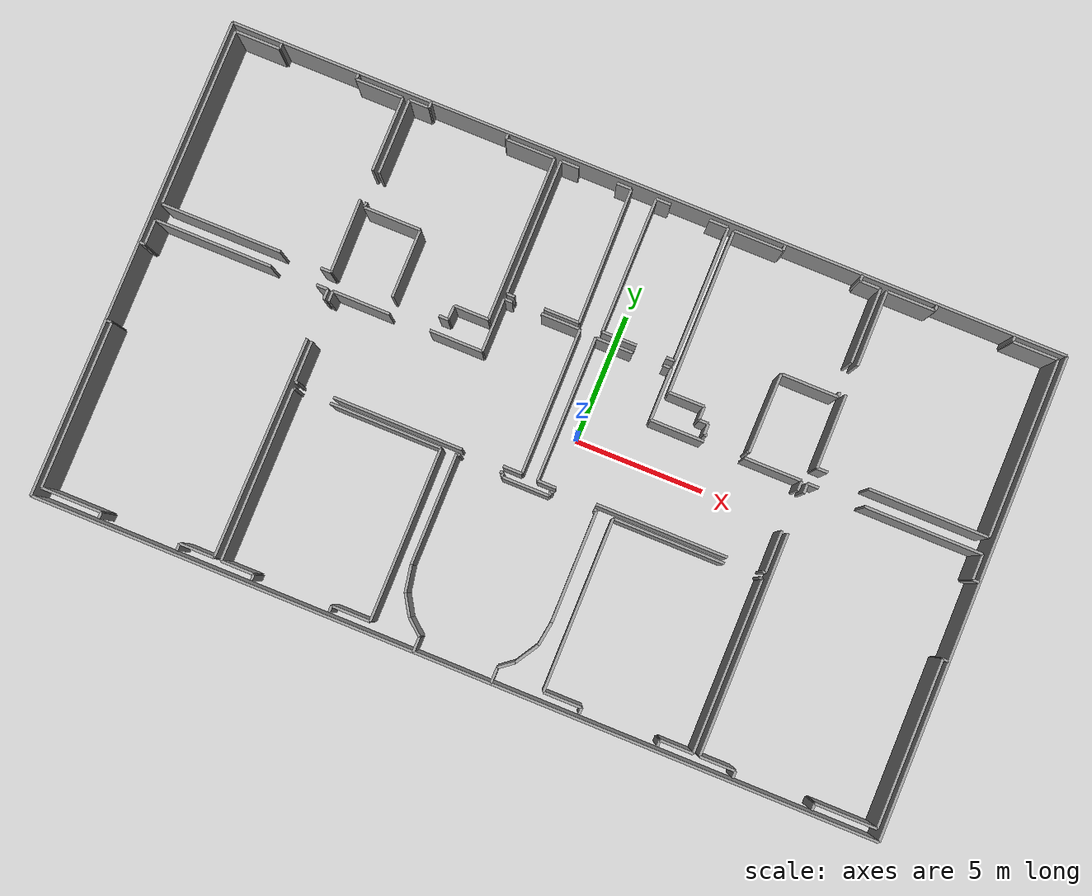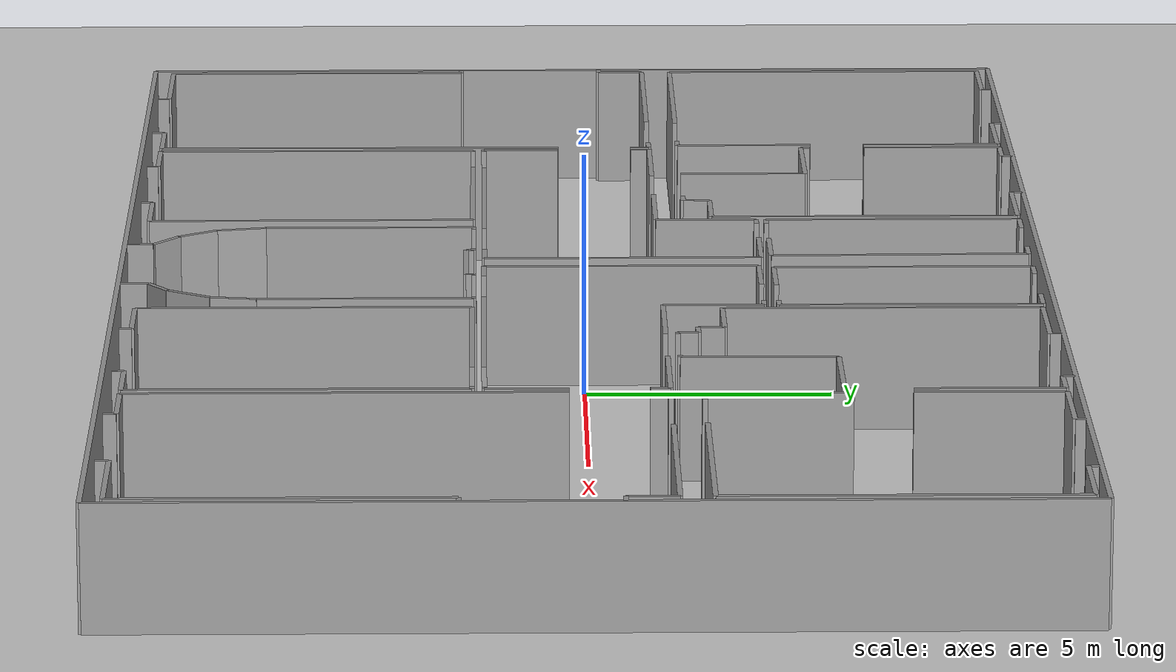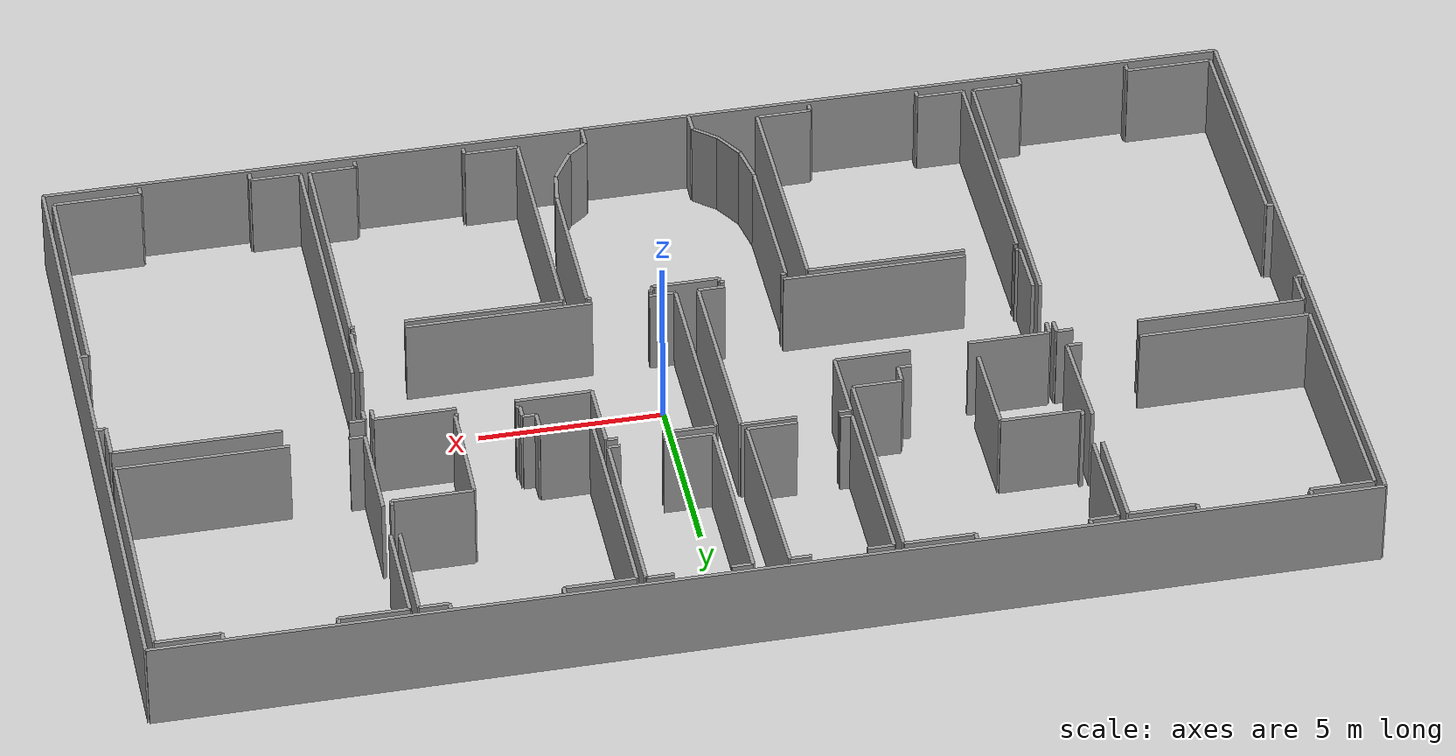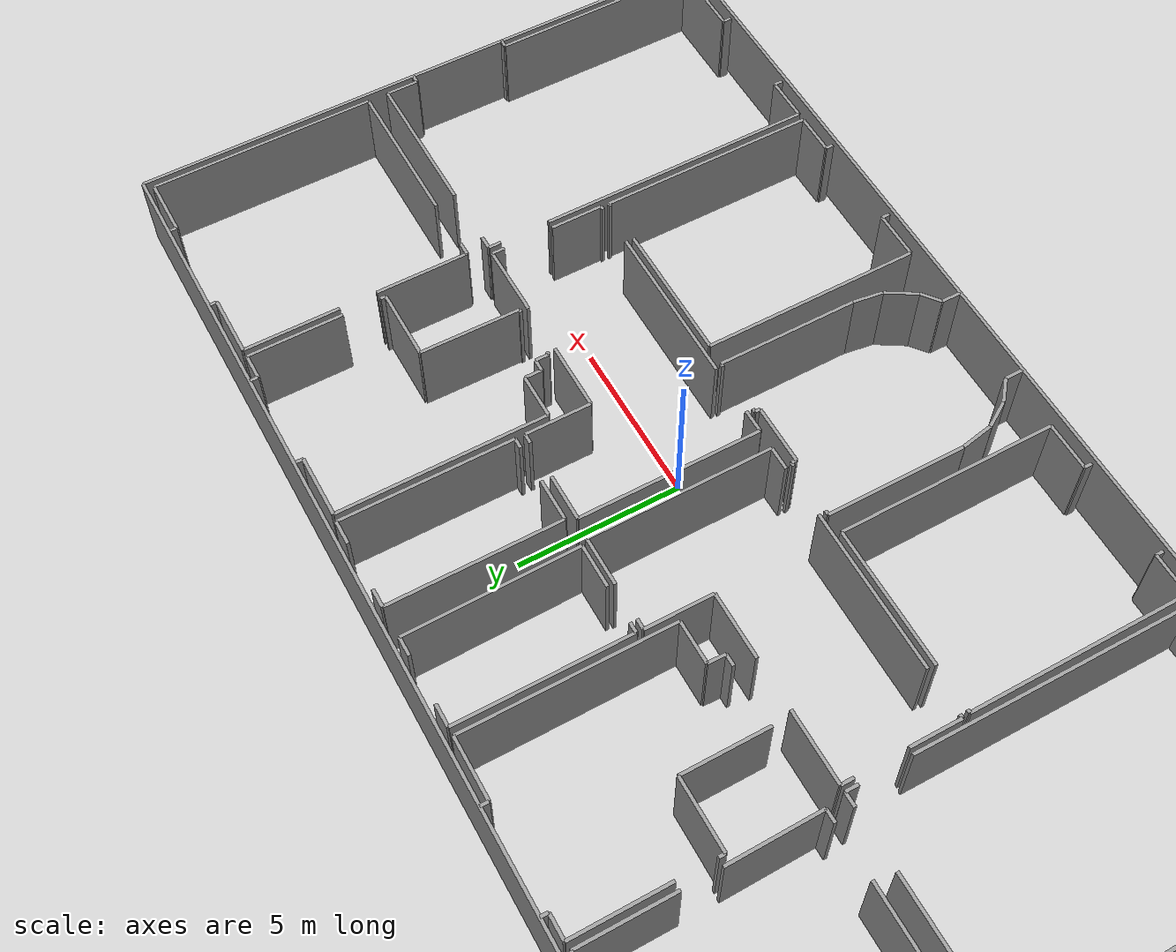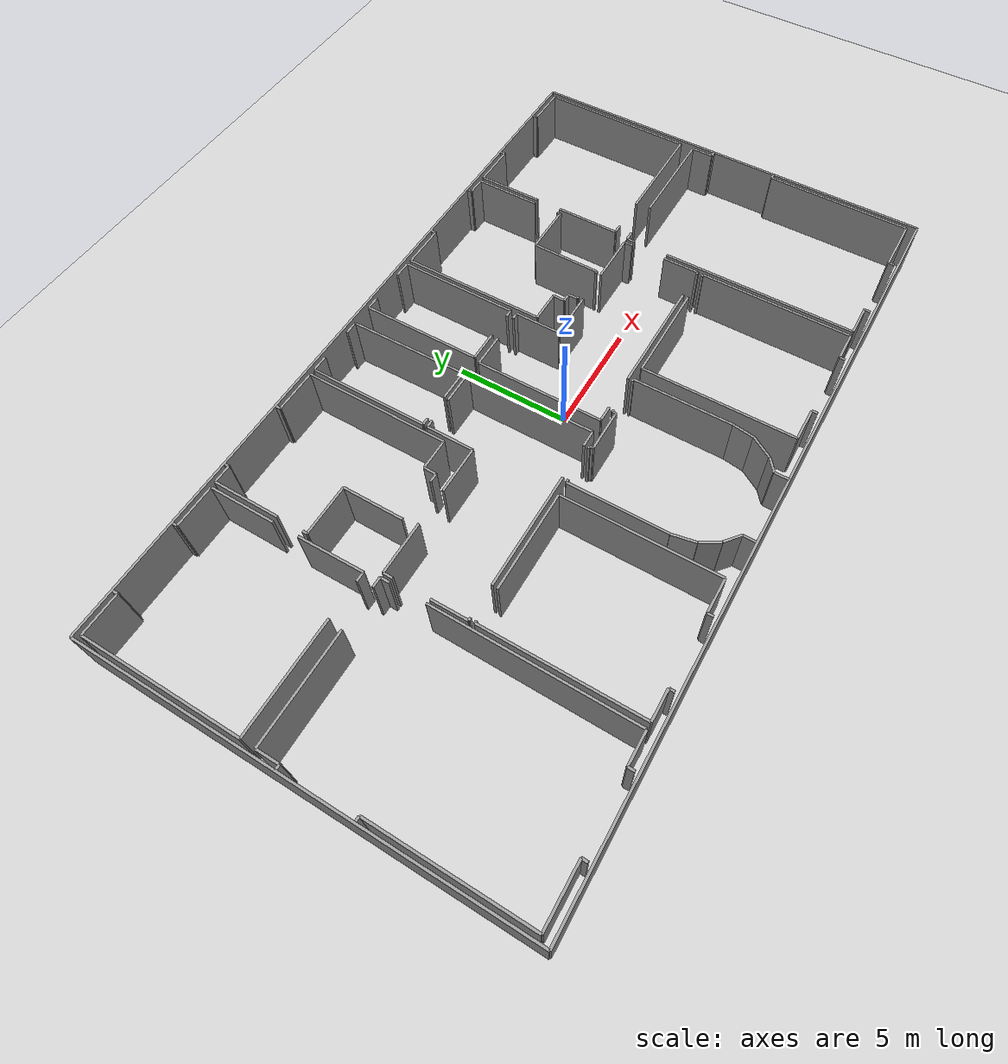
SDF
<sdf version="1.6">
  <world name="default">
    <light name="sun" type="directional">
      <cast_shadows>1</cast_shadows>
      <pose frame="">0 0 10 0 -0 0</pose>
      <diffuse>0.8 0.8 0.8 1</diffuse>
      <specular>0.1 0.1 0.1 1</specular>
      <attenuation>
        <range>1000</range>
        <constant>0.9</constant>
        <linear>0.01</linear>
        <quadratic>0.001</quadratic>
      </attenuation>
      <direction>-0.5 0.5 -1</direction>
    </light>
    <model name="ground_plane">
      <static>1</static>
      <link name="link">
        <collision name="collision">
          <geometry>
            <plane>
              <normal>0 0 1</normal>
              <size>100 100</size>
            </plane>
          </geometry>
          <surface>
            <friction>
              <ode>
                <mu>100</mu>
                <mu2>50</mu2>
              </ode>
              <torsional>
                <ode />
              </torsional>
            </friction>
            <contact>
              <ode />
            </contact>
            <bounce />
          </surface>
          <max_contacts>10</max_contacts>
        </collision>
        <visual name="visual">
          <cast_shadows>0</cast_shadows>
          <geometry>
            <plane>
              <normal>0 0 1</normal>
              <size>100 100</size>
            </plane>
          </geometry>
          <material>
            <script>
              <uri>file://media/materials/scripts/gazebo.material</uri>
              <name>Gazebo/Grey</name>
            </script>
          </material>
        </visual>
        <self_collide>0</self_collide>
        <kinematic>0</kinematic>
        <gravity>1</gravity>
      </link>
    </model>
    <gravity>0 0 -9.8</gravity>
    <magnetic_field>6e-06 2.3e-05 -4.2e-05</magnetic_field>
    <atmosphere type="adiabatic" />
    <physics default="0" name="default_physics" type="ode">
      <max_step_size>0.001</max_step_size>
      <real_time_factor>1</real_time_factor>
      <real_time_update_rate>1000</real_time_update_rate>
    </physics>
    <scene>
      <ambient>0.4 0.4 0.4 1</ambient>
      <background>0.7 0.7 0.7 1</background>
      <shadows>1</shadows>
    </scene>
    <spherical_coordinates>
      <surface_model>EARTH_WGS84</surface_model>
      <latitude_deg>0</latitude_deg>
      <longitude_deg>0</longitude_deg>
      <elevation>0</elevation>
      <heading_deg>0</heading_deg>
    </spherical_coordinates>
  <model name="0510034861_A-40">
		<static>1</static>
		<link name="Wall_0">
			<collision name="Wall_0_Collision">
				<geometry>
					<box>
						<size>0.40639932986 0.1 2.5</size>
					</box>
				</geometry>
				<pose frame="">0.20319966493 0 1.25 0 0 0</pose>
			</collision>
			<visual name="Wall_0_Visual">
				<pose frame="">0.20319966493 0 1.25 0 0 0</pose>
				<geometry>
					<box>
						<size>0.40639932986 0.1 2.5</size>
					</box>
				</geometry>
				<material>
					<script>
						<uri>file://media/materials/scripts/gazebo.material</uri>
						<name>Gazebo/Grey</name>
					</script>
					<ambient>1 1 1 1</ambient>
				</material>
			</visual>
			<pose frame="">6.86106651267 -7.14993749167 0 0 0 3.14159265359</pose>
		</link>
		<link name="Wall_1">
			<collision name="Wall_1_Collision">
				<geometry>
					<box>
						<size>4.65658495104 0.1 2.5</size>
					</box>
				</geometry>
				<pose frame="">2.32829247552 0 1.25 0 0 0</pose>
			</collision>
			<visual name="Wall_1_Visual">
				<pose frame="">2.32829247552 0 1.25 0 0 0</pose>
				<geometry>
					<box>
						<size>4.65658495104 0.1 2.5</size>
					</box>
				</geometry>
				<material>
					<script>
						<uri>file://media/materials/scripts/gazebo.material</uri>
						<name>Gazebo/Grey</name>
					</script>
					<ambient>1 1 1 1</ambient>
				</material>
			</visual>
			<pose frame="">4.88224953833 -7.14993749167 0 0 0 3.14159265359</pose>
		</link>
		<link name="Wall_2">
			<collision name="Wall_2_Collision">
				<geometry>
					<box>
						<size>6.88949669689 0.1 2.5</size>
					</box>
				</geometry>
				<pose frame="">3.44474834845 0 1.25 0 0 0</pose>
			</collision>
			<visual name="Wall_2_Visual">
				<pose frame="">3.44474834845 0 1.25 0 0 0</pose>
				<geometry>
					<box>
						<size>6.88949669689 0.1 2.5</size>
					</box>
				</geometry>
				<material>
					<script>
						<uri>file://media/materials/scripts/gazebo.material</uri>
						<name>Gazebo/Grey</name>
					</script>
					<ambient>1 1 1 1</ambient>
				</material>
			</visual>
			<pose frame="">0.225664587286 -7.14993749167 0 0 0 1.57079632679</pose>
		</link>
		<link name="Wall_3">
			<collision name="Wall_3_Collision">
				<geometry>
					<box>
						<size>1.7336066354 0.1 2.5</size>
					</box>
				</geometry>
				<pose frame="">0.866803317701 0 1.25 0 0 0</pose>
			</collision>
			<visual name="Wall_3_Visual">
				<pose frame="">0.866803317701 0 1.25 0 0 0</pose>
				<geometry>
					<box>
						<size>1.7336066354 0.1 2.5</size>
					</box>
				</geometry>
				<material>
					<script>
						<uri>file://media/materials/scripts/gazebo.material</uri>
						<name>Gazebo/Grey</name>
					</script>
					<ambient>1 1 1 1</ambient>
				</material>
			</visual>
			<pose frame="">0.225664587286 -0.260440794776 0 0 0 0.0</pose>
		</link>
		<link name="Wall_4">
			<collision name="Wall_4_Collision">
				<geometry>
					<box>
						<size>0.222110814258 0.1 2.5</size>
					</box>
				</geometry>
				<pose frame="">0.111055407129 0 1.25 0 0 0</pose>
			</collision>
			<visual name="Wall_4_Visual">
				<pose frame="">0.111055407129 0 1.25 0 0 0</pose>
				<geometry>
					<box>
						<size>0.222110814258 0.1 2.5</size>
					</box>
				</geometry>
				<material>
					<script>
						<uri>file://media/materials/scripts/gazebo.material</uri>
						<name>Gazebo/Grey</name>
					</script>
					<ambient>1 1 1 1</ambient>
				</material>
			</visual>
			<pose frame="">1.95927122269 -0.260440794776 0 0 0 1.57079632679</pose>
		</link>
		<link name="Wall_5">
			<collision name="Wall_5_Collision">
				<geometry>
					<box>
						<size>0.214114824945 0.1 2.5</size>
					</box>
				</geometry>
				<pose frame="">0.107057412472 0 1.25 0 0 0</pose>
			</collision>
			<visual name="Wall_5_Visual">
				<pose frame="">0.107057412472 0 1.25 0 0 0</pose>
				<geometry>
					<box>
						<size>0.214114824945 0.1 2.5</size>
					</box>
				</geometry>
				<material>
					<script>
						<uri>file://media/materials/scripts/gazebo.material</uri>
						<name>Gazebo/Grey</name>
					</script>
					<ambient>1 1 1 1</ambient>
				</material>
			</visual>
			<pose frame="">4.98937041103 -0.0383299805177 0 0 0 -1.57079632679</pose>
		</link>
		<link name="Wall_6">
			<collision name="Wall_6_Collision">
				<geometry>
					<box>
						<size>1.8381890988 0.1 2.5</size>
					</box>
				</geometry>
				<pose frame="">0.919094549401 0 1.25 0 0 0</pose>
			</collision>
			<visual name="Wall_6_Visual">
				<pose frame="">0.919094549401 0 1.25 0 0 0</pose>
				<geometry>
					<box>
						<size>1.8381890988 0.1 2.5</size>
					</box>
				</geometry>
				<material>
					<script>
						<uri>file://media/materials/scripts/gazebo.material</uri>
						<name>Gazebo/Grey</name>
					</script>
					<ambient>1 1 1 1</ambient>
				</material>
			</visual>
			<pose frame="">4.98937041103 -0.252444805463 0 0 0 0.0</pose>
		</link>
		<link name="Wall_7">
			<collision name="Wall_7_Collision">
				<geometry>
					<box>
						<size>2.89162896071 0.1 2.5</size>
					</box>
				</geometry>
				<pose frame="">1.44581448036 0 1.25 0 0 0</pose>
			</collision>
			<visual name="Wall_7_Visual">
				<pose frame="">1.44581448036 0 1.25 0 0 0</pose>
				<geometry>
					<box>
						<size>2.89162896071 0.1 2.5</size>
					</box>
				</geometry>
				<material>
					<script>
						<uri>file://media/materials/scripts/gazebo.material</uri>
						<name>Gazebo/Grey</name>
					</script>
					<ambient>1 1 1 1</ambient>
				</material>
			</visual>
			<pose frame="">6.82755950983 -0.252444805463 0 0 0 -1.57079632679</pose>
		</link>
		<link name="Wall_8">
			<collision name="Wall_8_Collision">
				<geometry>
					<box>
						<size>2.85869909492 0.1 2.5</size>
					</box>
				</geometry>
				<pose frame="">1.42934954746 0 1.25 0 0 0</pose>
			</collision>
			<visual name="Wall_8_Visual">
				<pose frame="">1.42934954746 0 1.25 0 0 0</pose>
				<geometry>
					<box>
						<size>2.85869909492 0.1 2.5</size>
					</box>
				</geometry>
				<material>
					<script>
						<uri>file://media/materials/scripts/gazebo.material</uri>
						<name>Gazebo/Grey</name>
					</script>
					<ambient>1 1 1 1</ambient>
				</material>
			</visual>
			<pose frame="">6.82755950983 -4.2914347724 0 0 0 -1.55907499167</pose>
		</link>
		<link name="Wall_9">
			<collision name="Wall_9_Collision">
				<geometry>
					<box>
						<size>0.364134814918 0.1 2.5</size>
					</box>
				</geometry>
				<pose frame="">0.182067407459 0 1.25 0 0 0</pose>
			</collision>
			<visual name="Wall_9_Visual">
				<pose frame="">0.182067407459 0 1.25 0 0 0</pose>
				<geometry>
					<box>
						<size>0.364134814918 0.1 2.5</size>
					</box>
				</geometry>
				<material>
					<script>
						<uri>file://media/materials/scripts/gazebo.material</uri>
						<name>Gazebo/Grey</name>
					</script>
					<ambient>1 1 1 1</ambient>
				</material>
			</visual>
			<pose frame="">11.4422607073 -7.14993749167 0 0 0 3.14159265359</pose>
		</link>
		<link name="Wall_10">
			<collision name="Wall_10_Collision">
				<geometry>
					<box>
						<size>2.64603786037 0.1 2.5</size>
					</box>
				</geometry>
				<pose frame="">1.32301893019 0 1.25 0 0 0</pose>
			</collision>
			<visual name="Wall_10_Visual">
				<pose frame="">1.32301893019 0 1.25 0 0 0</pose>
				<geometry>
					<box>
						<size>2.64603786037 0.1 2.5</size>
					</box>
				</geometry>
				<material>
					<script>
						<uri>file://media/materials/scripts/gazebo.material</uri>
						<name>Gazebo/Grey</name>
					</script>
					<ambient>1 1 1 1</ambient>
				</material>
			</visual>
			<pose frame="">9.26278247736 -7.14993749167 0 0 0 1.57079632679</pose>
		</link>
		<link name="Wall_11">
			<collision name="Wall_11_Collision">
				<geometry>
					<box>
						<size>2.18569733277 0.1 2.5</size>
					</box>
				</geometry>
				<pose frame="">1.09284866638 0 1.25 0 0 0</pose>
			</collision>
			<visual name="Wall_11_Visual">
				<pose frame="">1.09284866638 0 1.25 0 0 0</pose>
				<geometry>
					<box>
						<size>2.18569733277 0.1 2.5</size>
					</box>
				</geometry>
				<material>
					<script>
						<uri>file://media/materials/scripts/gazebo.material</uri>
						<name>Gazebo/Grey</name>
					</script>
					<ambient>1 1 1 1</ambient>
				</material>
			</visual>
			<pose frame="">9.26278247736 -4.5038996313 0 0 0 3.14159265359</pose>
		</link>
		<link name="Wall_12">
			<collision name="Wall_12_Collision">
				<geometry>
					<box>
						<size>0.195584437013 0.1 2.5</size>
					</box>
				</geometry>
				<pose frame="">0.0977922185063 0 1.25 0 0 0</pose>
			</collision>
			<visual name="Wall_12_Visual">
				<pose frame="">0.0977922185063 0 1.25 0 0 0</pose>
				<geometry>
					<box>
						<size>0.195584437013 0.1 2.5</size>
					</box>
				</geometry>
				<material>
					<script>
						<uri>file://media/materials/scripts/gazebo.material</uri>
						<name>Gazebo/Grey</name>
					</script>
					<ambient>1 1 1 1</ambient>
				</material>
			</visual>
			<pose frame="">7.07708514459 -4.5038996313 0 0 0 1.57079632679</pose>
		</link>
		<link name="Wall_13">
			<collision name="Wall_13_Collision">
				<geometry>
					<box>
						<size>2.91092087144 0.1 2.5</size>
					</box>
				</geometry>
				<pose frame="">1.45546043572 0 1.25 0 0 0</pose>
			</collision>
			<visual name="Wall_13_Visual">
				<pose frame="">1.45546043572 0 1.25 0 0 0</pose>
				<geometry>
					<box>
						<size>2.91092087144 0.1 2.5</size>
					</box>
				</geometry>
				<material>
					<script>
						<uri>file://media/materials/scripts/gazebo.material</uri>
						<name>Gazebo/Grey</name>
					</script>
					<ambient>1 1 1 1</ambient>
				</material>
			</visual>
			<pose frame="">7.07708514459 -3.1414084364 0 0 0 1.57079632679</pose>
		</link>
		<link name="Wall_14">
			<collision name="Wall_14_Collision">
				<geometry>
					<box>
						<size>0.771041826639 0.1 2.5</size>
					</box>
				</geometry>
				<pose frame="">0.38552091332 0 1.25 0 0 0</pose>
			</collision>
			<visual name="Wall_14_Visual">
				<pose frame="">0.38552091332 0 1.25 0 0 0</pose>
				<geometry>
					<box>
						<size>0.771041826639 0.1 2.5</size>
					</box>
				</geometry>
				<material>
					<script>
						<uri>file://media/materials/scripts/gazebo.material</uri>
						<name>Gazebo/Grey</name>
					</script>
					<ambient>1 1 1 1</ambient>
				</material>
			</visual>
			<pose frame="">7.07708514459 -0.230487564967 0 0 0 0.0</pose>
		</link>
		<link name="Wall_15">
			<collision name="Wall_15_Collision">
				<geometry>
					<box>
						<size>0.230487564967 0.1 2.5</size>
					</box>
				</geometry>
				<pose frame="">0.115243782484 0 1.25 0 0 0</pose>
			</collision>
			<visual name="Wall_15_Visual">
				<pose frame="">0.115243782484 0 1.25 0 0 0</pose>
				<geometry>
					<box>
						<size>0.230487564967 0.1 2.5</size>
					</box>
				</geometry>
				<material>
					<script>
						<uri>file://media/materials/scripts/gazebo.material</uri>
						<name>Gazebo/Grey</name>
					</script>
					<ambient>1 1 1 1</ambient>
				</material>
			</visual>
			<pose frame="">7.84812697123 -0.230487564967 0 0 0 1.57079632679</pose>
		</link>
		<link name="Wall_16">
			<collision name="Wall_16_Collision">
				<geometry>
					<box>
						<size>0.248129509643 0.1 2.5</size>
					</box>
				</geometry>
				<pose frame="">0.124064754821 0 1.25 0 0 0</pose>
			</collision>
			<visual name="Wall_16_Visual">
				<pose frame="">0.124064754821 0 1.25 0 0 0</pose>
				<geometry>
					<box>
						<size>0.248129509643 0.1 2.5</size>
					</box>
				</geometry>
				<material>
					<script>
						<uri>file://media/materials/scripts/gazebo.material</uri>
						<name>Gazebo/Grey</name>
					</script>
					<ambient>1 1 1 1</ambient>
				</material>
			</visual>
			<pose frame="">10.8825414554 -0.0 0 0 0 -1.57079632679</pose>
		</link>
		<link name="Wall_17">
			<collision name="Wall_17_Collision">
				<geometry>
					<box>
						<size>1.90380697936 0.1 2.5</size>
					</box>
				</geometry>
				<pose frame="">0.951903489678 0 1.25 0 0 0</pose>
			</collision>
			<visual name="Wall_17_Visual">
				<pose frame="">0.951903489678 0 1.25 0 0 0</pose>
				<geometry>
					<box>
						<size>1.90380697936 0.1 2.5</size>
					</box>
				</geometry>
				<material>
					<script>
						<uri>file://media/materials/scripts/gazebo.material</uri>
						<name>Gazebo/Grey</name>
					</script>
					<ambient>1 1 1 1</ambient>
				</material>
			</visual>
			<pose frame="">10.8825414554 -0.248129509643 0 0 0 0.0</pose>
		</link>
		<link name="Wall_18">
			<collision name="Wall_18_Collision">
				<geometry>
					<box>
						<size>6.35541537895 0.1 2.5</size>
					</box>
				</geometry>
				<pose frame="">3.17770768948 0 1.25 0 0 0</pose>
			</collision>
			<visual name="Wall_18_Visual">
				<pose frame="">3.17770768948 0 1.25 0 0 0</pose>
				<geometry>
					<box>
						<size>6.35541537895 0.1 2.5</size>
					</box>
				</geometry>
				<material>
					<script>
						<uri>file://media/materials/scripts/gazebo.material</uri>
						<name>Gazebo/Grey</name>
					</script>
					<ambient>1 1 1 1</ambient>
				</material>
			</visual>
			<pose frame="">12.7863484348 -0.248129509643 0 0 0 -1.57079632679</pose>
		</link>
		<link name="Wall_19">
			<collision name="Wall_19_Collision">
				<geometry>
					<box>
						<size>1.32644578275 0.1 2.5</size>
					</box>
				</geometry>
				<pose frame="">0.663222891375 0 1.25 0 0 0</pose>
			</collision>
			<visual name="Wall_19_Visual">
				<pose frame="">0.663222891375 0 1.25 0 0 0</pose>
				<geometry>
					<box>
						<size>1.32644578275 0.1 2.5</size>
					</box>
				</geometry>
				<material>
					<script>
						<uri>file://media/materials/scripts/gazebo.material</uri>
						<name>Gazebo/Grey</name>
					</script>
					<ambient>1 1 1 1</ambient>
				</material>
			</visual>
			<pose frame="">12.7863484348 -6.6035448886 0 0 0 3.14159265359</pose>
		</link>
		<link name="Wall_20">
			<collision name="Wall_20_Collision">
				<geometry>
					<box>
						<size>0.546677340766 0.1 2.5</size>
					</box>
				</geometry>
				<pose frame="">0.273338670383 0 1.25 0 0 0</pose>
			</collision>
			<visual name="Wall_20_Visual">
				<pose frame="">0.273338670383 0 1.25 0 0 0</pose>
				<geometry>
					<box>
						<size>0.546677340766 0.1 2.5</size>
					</box>
				</geometry>
				<material>
					<script>
						<uri>file://media/materials/scripts/gazebo.material</uri>
						<name>Gazebo/Grey</name>
					</script>
					<ambient>1 1 1 1</ambient>
				</material>
			</visual>
			<pose frame="">11.459902652 -6.6035448886 0 0 0 -1.60307315069</pose>
		</link>
		<link name="Wall_21">
			<collision name="Wall_21_Collision">
				<geometry>
					<box>
						<size>1.3555105693 0.1 2.5</size>
					</box>
				</geometry>
				<pose frame="">0.677755284651 0 1.25 0 0 0</pose>
			</collision>
			<visual name="Wall_21_Visual">
				<pose frame="">0.677755284651 0 1.25 0 0 0</pose>
				<geometry>
					<box>
						<size>1.3555105693 0.1 2.5</size>
					</box>
				</geometry>
				<material>
					<script>
						<uri>file://media/materials/scripts/gazebo.material</uri>
						<name>Gazebo/Grey</name>
					</script>
					<ambient>1 1 1 1</ambient>
				</material>
			</visual>
			<pose frame="">15.8645504794 -5.48499482799 0 0 0 3.14159265359</pose>
		</link>
		<link name="Wall_22">
			<collision name="Wall_22_Collision">
				<geometry>
					<box>
						<size>0.316793481365 0.1 2.5</size>
					</box>
				</geometry>
				<pose frame="">0.158396740682 0 1.25 0 0 0</pose>
			</collision>
			<visual name="Wall_22_Visual">
				<pose frame="">0.158396740682 0 1.25 0 0 0</pose>
				<geometry>
					<box>
						<size>0.316793481365 0.1 2.5</size>
					</box>
				</geometry>
				<material>
					<script>
						<uri>file://media/materials/scripts/gazebo.material</uri>
						<name>Gazebo/Grey</name>
					</script>
					<ambient>1 1 1 1</ambient>
				</material>
			</visual>
			<pose frame="">13.3590135741 -5.48499482799 0 0 0 3.14159265359</pose>
		</link>
		<link name="Wall_23">
			<collision name="Wall_23_Collision">
				<geometry>
					<box>
						<size>5.2447343872 0.1 2.5</size>
					</box>
				</geometry>
				<pose frame="">2.6223671936 0 1.25 0 0 0</pose>
			</collision>
			<visual name="Wall_23_Visual">
				<pose frame="">2.6223671936 0 1.25 0 0 0</pose>
				<geometry>
					<box>
						<size>5.2447343872 0.1 2.5</size>
					</box>
				</geometry>
				<material>
					<script>
						<uri>file://media/materials/scripts/gazebo.material</uri>
						<name>Gazebo/Grey</name>
					</script>
					<ambient>1 1 1 1</ambient>
				</material>
			</visual>
			<pose frame="">13.0422200928 -5.48499482799 0 0 0 1.57079632679</pose>
		</link>
		<link name="Wall_24">
			<collision name="Wall_24_Collision">
				<geometry>
					<box>
						<size>0.703266298174 0.1 2.5</size>
					</box>
				</geometry>
				<pose frame="">0.351633149087 0 1.25 0 0 0</pose>
			</collision>
			<visual name="Wall_24_Visual">
				<pose frame="">0.351633149087 0 1.25 0 0 0</pose>
				<geometry>
					<box>
						<size>0.703266298174 0.1 2.5</size>
					</box>
				</geometry>
				<material>
					<script>
						<uri>file://media/materials/scripts/gazebo.material</uri>
						<name>Gazebo/Grey</name>
					</script>
					<ambient>1 1 1 1</ambient>
				</material>
			</visual>
			<pose frame="">13.0422200928 -0.240260440795 0 0 0 0.0</pose>
		</link>
		<link name="Wall_25">
			<collision name="Wall_25_Collision">
				<geometry>
					<box>
						<size>0.572538218925 0.1 2.5</size>
					</box>
				</geometry>
				<pose frame="">0.286269109463 0 1.25 0 0 0</pose>
			</collision>
			<visual name="Wall_25_Visual">
				<pose frame="">0.286269109463 0 1.25 0 0 0</pose>
				<geometry>
					<box>
						<size>0.572538218925 0.1 2.5</size>
					</box>
				</geometry>
				<material>
					<script>
						<uri>file://media/materials/scripts/gazebo.material</uri>
						<name>Gazebo/Grey</name>
					</script>
					<ambient>1 1 1 1</ambient>
				</material>
			</visual>
			<pose frame="">15.2197945158 -0.240260440795 0 0 0 0.0</pose>
		</link>
		<link name="Wall_26">
			<collision name="Wall_26_Collision">
				<geometry>
					<box>
						<size>5.24523156733 0.1 2.5</size>
					</box>
				</geometry>
				<pose frame="">2.62261578366 0 1.25 0 0 0</pose>
			</collision>
			<visual name="Wall_26_Visual">
				<pose frame="">2.62261578366 0 1.25 0 0 0</pose>
				<geometry>
					<box>
						<size>5.24523156733 0.1 2.5</size>
					</box>
				</geometry>
				<material>
					<script>
						<uri>file://media/materials/scripts/gazebo.material</uri>
						<name>Gazebo/Grey</name>
					</script>
					<ambient>1 1 1 1</ambient>
				</material>
			</visual>
			<pose frame="">15.7923327347 -0.240260440795 0 0 0 -1.55702762551</pose>
		</link>
		<link name="Wall_27">
			<collision name="Wall_27_Collision">
				<geometry>
					<box>
						<size>1.34078779533 0.1 2.5</size>
					</box>
				</geometry>
				<pose frame="">0.670393897664 0 1.25 0 0 0</pose>
			</collision>
			<visual name="Wall_27_Visual">
				<pose frame="">0.670393897664 0 1.25 0 0 0</pose>
				<geometry>
					<box>
						<size>1.34078779533 0.1 2.5</size>
					</box>
				</geometry>
				<material>
					<script>
						<uri>file://media/materials/scripts/gazebo.material</uri>
						<name>Gazebo/Grey</name>
					</script>
					<ambient>1 1 1 1</ambient>
				</material>
			</visual>
			<pose frame="">6.9447070993 -18.2281903045 0 0 0 3.14159265359</pose>
		</link>
		<link name="Wall_28">
			<collision name="Wall_28_Collision">
				<geometry>
					<box>
						<size>0.268817545485 0.1 2.5</size>
					</box>
				</geometry>
				<pose frame="">0.134408772743 0 1.25 0 0 0</pose>
			</collision>
			<visual name="Wall_28_Visual">
				<pose frame="">0.134408772743 0 1.25 0 0 0</pose>
				<geometry>
					<box>
						<size>0.268817545485 0.1 2.5</size>
					</box>
				</geometry>
				<material>
					<script>
						<uri>file://media/materials/scripts/gazebo.material</uri>
						<name>Gazebo/Grey</name>
					</script>
					<ambient>1 1 1 1</ambient>
				</material>
			</visual>
			<pose frame="">5.60391930397 -18.2281903045 0 0 0 -1.57079632679</pose>
		</link>
		<link name="Wall_29">
			<collision name="Wall_29_Collision">
				<geometry>
					<box>
						<size>0.24686030499 0.1 2.5</size>
					</box>
				</geometry>
				<pose frame="">0.123430152495 0 1.25 0 0 0</pose>
			</collision>
			<visual name="Wall_29_Visual">
				<pose frame="">0.123430152495 0 1.25 0 0 0</pose>
				<geometry>
					<box>
						<size>0.24686030499 0.1 2.5</size>
					</box>
				</geometry>
				<material>
					<script>
						<uri>file://media/materials/scripts/gazebo.material</uri>
						<name>Gazebo/Grey</name>
					</script>
					<ambient>1 1 1 1</ambient>
				</material>
			</visual>
			<pose frame="">2.57508932028 -18.49700785 0 0 0 1.57079632679</pose>
		</link>
		<link name="Wall_30">
			<collision name="Wall_30_Collision">
				<geometry>
					<box>
						<size>2.33749420925 0.1 2.5</size>
					</box>
				</geometry>
				<pose frame="">1.16874710463 0 1.25 0 0 0</pose>
			</collision>
			<visual name="Wall_30_Visual">
				<pose frame="">1.16874710463 0 1.25 0 0 0</pose>
				<geometry>
					<box>
						<size>2.33749420925 0.1 2.5</size>
					</box>
				</geometry>
				<material>
					<script>
						<uri>file://media/materials/scripts/gazebo.material</uri>
						<name>Gazebo/Grey</name>
					</script>
					<ambient>1 1 1 1</ambient>
				</material>
			</visual>
			<pose frame="">2.57508932028 -18.250147545 0 0 0 3.14159265359</pose>
		</link>
		<link name="Wall_31">
			<collision name="Wall_31_Collision">
				<geometry>
					<box>
						<size>6.43689831767 0.1 2.5</size>
					</box>
				</geometry>
				<pose frame="">3.21844915883 0 1.25 0 0 0</pose>
			</collision>
			<visual name="Wall_31_Visual">
				<pose frame="">3.21844915883 0 1.25 0 0 0</pose>
				<geometry>
					<box>
						<size>6.43689831767 0.1 2.5</size>
					</box>
				</geometry>
				<material>
					<script>
						<uri>file://media/materials/scripts/gazebo.material</uri>
						<name>Gazebo/Grey</name>
					</script>
					<ambient>1 1 1 1</ambient>
				</material>
			</visual>
			<pose frame="">0.237595111024 -18.250147545 0 0 0 1.57079632679</pose>
		</link>
		<link name="Wall_32">
			<collision name="Wall_32_Collision">
				<geometry>
					<box>
						<size>0.237595111024 0.1 2.5</size>
					</box>
				</geometry>
				<pose frame="">0.118797555512 0 1.25 0 0 0</pose>
			</collision>
			<visual name="Wall_32_Visual">
				<pose frame="">0.118797555512 0 1.25 0 0 0</pose>
				<geometry>
					<box>
						<size>0.237595111024 0.1 2.5</size>
					</box>
				</geometry>
				<material>
					<script>
						<uri>file://media/materials/scripts/gazebo.material</uri>
						<name>Gazebo/Grey</name>
					</script>
					<ambient>1 1 1 1</ambient>
				</material>
			</visual>
			<pose frame="">0.237595111024 -11.8132492274 0 0 0 3.14159265359</pose>
		</link>
		<link name="Wall_33">
			<collision name="Wall_33_Collision">
				<geometry>
					<box>
						<size>0.224903064495 0.1 2.5</size>
					</box>
				</geometry>
				<pose frame="">0.112451532247 0 1.25 0 0 0</pose>
			</collision>
			<visual name="Wall_33_Visual">
				<pose frame="">0.112451532247 0 1.25 0 0 0</pose>
				<geometry>
					<box>
						<size>0.224903064495 0.1 2.5</size>
					</box>
				</geometry>
				<material>
					<script>
						<uri>file://media/materials/scripts/gazebo.material</uri>
						<name>Gazebo/Grey</name>
					</script>
					<ambient>1 1 1 1</ambient>
				</material>
			</visual>
			<pose frame="">0.0 -8.74355085386 0 0 0 0.0</pose>
		</link>
		<link name="Wall_34">
			<collision name="Wall_34_Collision">
				<geometry>
					<box>
						<size>0.97233768459 0.1 2.5</size>
					</box>
				</geometry>
				<pose frame="">0.486168842295 0 1.25 0 0 0</pose>
			</collision>
			<visual name="Wall_34_Visual">
				<pose frame="">0.486168842295 0 1.25 0 0 0</pose>
				<geometry>
					<box>
						<size>0.97233768459 0.1 2.5</size>
					</box>
				</geometry>
				<material>
					<script>
						<uri>file://media/materials/scripts/gazebo.material</uri>
						<name>Gazebo/Grey</name>
					</script>
					<ambient>1 1 1 1</ambient>
				</material>
			</visual>
			<pose frame="">0.224903064495 -8.74355085386 0 0 0 1.57079632679</pose>
		</link>
		<link name="Wall_35">
			<collision name="Wall_35_Collision">
				<geometry>
					<box>
						<size>4.55022560113 0.1 2.5</size>
					</box>
				</geometry>
				<pose frame="">2.27511280056 0 1.25 0 0 0</pose>
			</collision>
			<visual name="Wall_35_Visual">
				<pose frame="">2.27511280056 0 1.25 0 0 0</pose>
				<geometry>
					<box>
						<size>4.55022560113 0.1 2.5</size>
					</box>
				</geometry>
				<material>
					<script>
						<uri>file://media/materials/scripts/gazebo.material</uri>
						<name>Gazebo/Grey</name>
					</script>
					<ambient>1 1 1 1</ambient>
				</material>
			</visual>
			<pose frame="">0.224903064495 -7.77121316927 0 0 0 0.0</pose>
		</link>
		<link name="Wall_36">
			<collision name="Wall_36_Collision">
				<geometry>
					<box>
						<size>0.44142937828 0.1 2.5</size>
					</box>
				</geometry>
				<pose frame="">0.22071468914 0 1.25 0 0 0</pose>
			</collision>
			<visual name="Wall_36_Visual">
				<pose frame="">0.22071468914 0 1.25 0 0 0</pose>
				<geometry>
					<box>
						<size>0.44142937828 0.1 2.5</size>
					</box>
				</geometry>
				<material>
					<script>
						<uri>file://media/materials/scripts/gazebo.material</uri>
						<name>Gazebo/Grey</name>
					</script>
					<ambient>1 1 1 1</ambient>
				</material>
			</visual>
			<pose frame="">6.55468050946 -7.77121316927 0 0 0 0.0</pose>
		</link>
		<link name="Wall_37">
			<collision name="Wall_37_Collision">
				<geometry>
					<box>
						<size>0.39129579449 0.1 2.5</size>
					</box>
				</geometry>
				<pose frame="">0.195647897245 0 1.25 0 0 0</pose>
			</collision>
			<visual name="Wall_37_Visual">
				<pose frame="">0.195647897245 0 1.25 0 0 0</pose>
				<geometry>
					<box>
						<size>0.39129579449 0.1 2.5</size>
					</box>
				</geometry>
				<material>
					<script>
						<uri>file://media/materials/scripts/gazebo.material</uri>
						<name>Gazebo/Grey</name>
					</script>
					<ambient>1 1 1 1</ambient>
				</material>
			</visual>
			<pose frame="">6.99610988774 -7.77121316927 0 0 0 -1.57079632679</pose>
		</link>
		<link name="Wall_38">
			<collision name="Wall_38_Collision">
				<geometry>
					<box>
						<size>8.52070664632 0.1 2.5</size>
					</box>
				</geometry>
				<pose frame="">4.26035332316 0 1.25 0 0 0</pose>
			</collision>
			<visual name="Wall_38_Visual">
				<pose frame="">4.26035332316 0 1.25 0 0 0</pose>
				<geometry>
					<box>
						<size>8.52070664632 0.1 2.5</size>
					</box>
				</geometry>
				<material>
					<script>
						<uri>file://media/materials/scripts/gazebo.material</uri>
						<name>Gazebo/Grey</name>
					</script>
					<ambient>1 1 1 1</ambient>
				</material>
			</visual>
			<pose frame="">6.99610988774 -9.7076387082 0 0 0 -1.57682905417</pose>
		</link>
		<link name="Wall_39">
			<collision name="Wall_39_Collision">
				<geometry>
					<box>
						<size>1.48573096669 0.1 2.5</size>
					</box>
				</geometry>
				<pose frame="">0.742865483345 0 1.25 0 0 0</pose>
			</collision>
			<visual name="Wall_39_Visual">
				<pose frame="">0.742865483345 0 1.25 0 0 0</pose>
				<geometry>
					<box>
						<size>1.48573096669 0.1 2.5</size>
					</box>
				</geometry>
				<material>
					<script>
						<uri>file://media/materials/scripts/gazebo.material</uri>
						<name>Gazebo/Grey</name>
					</script>
					<ambient>1 1 1 1</ambient>
				</material>
			</visual>
			<pose frame="">12.9821867127 -18.2354247711 0 0 0 3.14159265359</pose>
		</link>
		<link name="Wall_40">
			<collision name="Wall_40_Collision">
				<geometry>
					<box>
						<size>0.24038736126 0.1 2.5</size>
					</box>
				</geometry>
				<pose frame="">0.12019368063 0 1.25 0 0 0</pose>
			</collision>
			<visual name="Wall_40_Visual">
				<pose frame="">0.12019368063 0 1.25 0 0 0</pose>
				<geometry>
					<box>
						<size>0.24038736126 0.1 2.5</size>
					</box>
				</geometry>
				<material>
					<script>
						<uri>file://media/materials/scripts/gazebo.material</uri>
						<name>Gazebo/Grey</name>
					</script>
					<ambient>1 1 1 1</ambient>
				</material>
			</visual>
			<pose frame="">11.496455746 -18.2354247711 0 0 0 -1.57079632679</pose>
		</link>
		<link name="Wall_41">
			<collision name="Wall_41_Collision">
				<geometry>
					<box>
						<size>0.230868326363 0.1 2.5</size>
					</box>
				</geometry>
				<pose frame="">0.115434163182 0 1.25 0 0 0</pose>
			</collision>
			<visual name="Wall_41_Visual">
				<pose frame="">0.115434163182 0 1.25 0 0 0</pose>
				<geometry>
					<box>
						<size>0.230868326363 0.1 2.5</size>
					</box>
				</geometry>
				<material>
					<script>
						<uri>file://media/materials/scripts/gazebo.material</uri>
						<name>Gazebo/Grey</name>
					</script>
					<ambient>1 1 1 1</ambient>
				</material>
			</visual>
			<pose frame="">8.49097912793 -18.4758121323 0 0 0 1.57079632679</pose>
		</link>
		<link name="Wall_42">
			<collision name="Wall_42_Collision">
				<geometry>
					<box>
						<size>1.2699661757 0.1 2.5</size>
					</box>
				</geometry>
				<pose frame="">0.634983087848 0 1.25 0 0 0</pose>
			</collision>
			<visual name="Wall_42_Visual">
				<pose frame="">0.634983087848 0 1.25 0 0 0</pose>
				<geometry>
					<box>
						<size>1.2699661757 0.1 2.5</size>
					</box>
				</geometry>
				<material>
					<script>
						<uri>file://media/materials/scripts/gazebo.material</uri>
						<name>Gazebo/Grey</name>
					</script>
					<ambient>1 1 1 1</ambient>
				</material>
			</visual>
			<pose frame="">8.49097912793 -18.244943806 0 0 0 3.14159265359</pose>
		</link>
		<link name="Wall_43">
			<collision name="Wall_43_Collision">
				<geometry>
					<box>
						<size>6.69683143058 0.1 2.5</size>
					</box>
				</geometry>
				<pose frame="">3.34841571529 0 1.25 0 0 0</pose>
			</collision>
			<visual name="Wall_43_Visual">
				<pose frame="">3.34841571529 0 1.25 0 0 0</pose>
				<geometry>
					<box>
						<size>6.69683143058 0.1 2.5</size>
					</box>
				</geometry>
				<material>
					<script>
						<uri>file://media/materials/scripts/gazebo.material</uri>
						<name>Gazebo/Grey</name>
					</script>
					<ambient>1 1 1 1</ambient>
				</material>
			</visual>
			<pose frame="">7.22101295223 -18.244943806 0 0 0 1.57079632679</pose>
		</link>
		<link name="Wall_44">
			<collision name="Wall_44_Collision">
				<geometry>
					<box>
						<size>0.100647928975 0.1 2.5</size>
					</box>
				</geometry>
				<pose frame="">0.0503239644877 0 1.25 0 0 0</pose>
			</collision>
			<visual name="Wall_44_Visual">
				<pose frame="">0.0503239644877 0 1.25 0 0 0</pose>
				<geometry>
					<box>
						<size>0.100647928975 0.1 2.5</size>
					</box>
				</geometry>
				<material>
					<script>
						<uri>file://media/materials/scripts/gazebo.material</uri>
						<name>Gazebo/Grey</name>
					</script>
					<ambient>1 1 1 1</ambient>
				</material>
			</visual>
			<pose frame="">7.22101295223 -11.5481123754 0 0 0 0.0</pose>
		</link>
		<link name="Wall_45">
			<collision name="Wall_45_Collision">
				<geometry>
					<box>
						<size>4.31047284219 0.1 2.5</size>
					</box>
				</geometry>
				<pose frame="">2.1552364211 0 1.25 0 0 0</pose>
			</collision>
			<visual name="Wall_45_Visual">
				<pose frame="">2.1552364211 0 1.25 0 0 0</pose>
				<geometry>
					<box>
						<size>4.31047284219 0.1 2.5</size>
					</box>
				</geometry>
				<material>
					<script>
						<uri>file://media/materials/scripts/gazebo.material</uri>
						<name>Gazebo/Grey</name>
					</script>
					<ambient>1 1 1 1</ambient>
				</material>
			</visual>
			<pose frame="">8.65724493746 -11.5481123754 0 0 0 0.0</pose>
		</link>
		<link name="Wall_46">
			<collision name="Wall_46_Collision">
				<geometry>
					<box>
						<size>6.68732804845 0.1 2.5</size>
					</box>
				</geometry>
				<pose frame="">3.34366402422 0 1.25 0 0 0</pose>
			</collision>
			<visual name="Wall_46_Visual">
				<pose frame="">3.34366402422 0 1.25 0 0 0</pose>
				<geometry>
					<box>
						<size>6.68732804845 0.1 2.5</size>
					</box>
				</geometry>
				<material>
					<script>
						<uri>file://media/materials/scripts/gazebo.material</uri>
						<name>Gazebo/Grey</name>
					</script>
					<ambient>1 1 1 1</ambient>
				</material>
			</visual>
			<pose frame="">12.9677177797 -11.5481123754 0 0 0 -1.5686326907</pose>
		</link>
		<link name="Wall_47">
			<collision name="Wall_47_Collision">
				<geometry>
					<box>
						<size>0.725096618204 0.1 2.5</size>
					</box>
				</geometry>
				<pose frame="">0.362548309102 0 1.25 0 0 0</pose>
			</collision>
			<visual name="Wall_47_Visual">
				<pose frame="">0.362548309102 0 1.25 0 0 0</pose>
				<geometry>
					<box>
						<size>0.725096618204 0.1 2.5</size>
					</box>
				</geometry>
				<material>
					<script>
						<uri>file://media/materials/scripts/gazebo.material</uri>
						<name>Gazebo/Grey</name>
					</script>
					<ambient>1 1 1 1</ambient>
				</material>
			</visual>
			<pose frame="">16.0083513666 -11.3125479918 0 0 0 3.14159265359</pose>
		</link>
		<link name="Wall_48">
			<collision name="Wall_48_Collision">
				<geometry>
					<box>
						<size>4.99876252546 0.1 2.5</size>
					</box>
				</geometry>
				<pose frame="">2.49938126273 0 1.25 0 0 0</pose>
			</collision>
			<visual name="Wall_48_Visual">
				<pose frame="">2.49938126273 0 1.25 0 0 0</pose>
				<geometry>
					<box>
						<size>4.99876252546 0.1 2.5</size>
					</box>
				</geometry>
				<material>
					<script>
						<uri>file://media/materials/scripts/gazebo.material</uri>
						<name>Gazebo/Grey</name>
					</script>
					<ambient>1 1 1 1</ambient>
				</material>
			</visual>
			<pose frame="">13.6864683746 -11.3125479918 0 0 0 3.14159265359</pose>
		</link>
		<link name="Wall_49">
			<collision name="Wall_49_Collision">
				<geometry>
					<box>
						<size>0.12476281738 0.1 2.5</size>
					</box>
				</geometry>
				<pose frame="">0.0623814086902 0 1.25 0 0 0</pose>
			</collision>
			<visual name="Wall_49_Visual">
				<pose frame="">0.0623814086902 0 1.25 0 0 0</pose>
				<geometry>
					<box>
						<size>0.12476281738 0.1 2.5</size>
					</box>
				</geometry>
				<material>
					<script>
						<uri>file://media/materials/scripts/gazebo.material</uri>
						<name>Gazebo/Grey</name>
					</script>
					<ambient>1 1 1 1</ambient>
				</material>
			</visual>
			<pose frame="">7.31277644864 -11.3125479918 0 0 0 3.14159265359</pose>
		</link>
		<link name="Wall_50">
			<collision name="Wall_50_Collision">
				<geometry>
					<box>
						<size>1.57609833798 0.1 2.5</size>
					</box>
				</geometry>
				<pose frame="">0.788049168988 0 1.25 0 0 0</pose>
			</collision>
			<visual name="Wall_50_Visual">
				<pose frame="">0.788049168988 0 1.25 0 0 0</pose>
				<geometry>
					<box>
						<size>1.57609833798 0.1 2.5</size>
					</box>
				</geometry>
				<material>
					<script>
						<uri>file://media/materials/scripts/gazebo.material</uri>
						<name>Gazebo/Grey</name>
					</script>
					<ambient>1 1 1 1</ambient>
				</material>
			</visual>
			<pose frame="">7.18801363126 -11.3125479918 0 0 0 1.57079632679</pose>
		</link>
		<link name="Wall_51">
			<collision name="Wall_51_Collision">
				<geometry>
					<box>
						<size>0.399037942873 0.1 2.5</size>
					</box>
				</geometry>
				<pose frame="">0.199518971437 0 1.25 0 0 0</pose>
			</collision>
			<visual name="Wall_51_Visual">
				<pose frame="">0.199518971437 0 1.25 0 0 0</pose>
				<geometry>
					<box>
						<size>0.399037942873 0.1 2.5</size>
					</box>
				</geometry>
				<material>
					<script>
						<uri>file://media/materials/scripts/gazebo.material</uri>
						<name>Gazebo/Grey</name>
					</script>
					<ambient>1 1 1 1</ambient>
				</material>
			</visual>
			<pose frame="">7.18801363126 -8.16301664562 0 0 0 1.57079632679</pose>
		</link>
		<link name="Wall_52">
			<collision name="Wall_52_Collision">
				<geometry>
					<box>
						<size>2.2166659263 0.1 2.5</size>
					</box>
				</geometry>
				<pose frame="">1.10833296315 0 1.25 0 0 0</pose>
			</collision>
			<visual name="Wall_52_Visual">
				<pose frame="">1.10833296315 0 1.25 0 0 0</pose>
				<geometry>
					<box>
						<size>2.2166659263 0.1 2.5</size>
					</box>
				</geometry>
				<material>
					<script>
						<uri>file://media/materials/scripts/gazebo.material</uri>
						<name>Gazebo/Grey</name>
					</script>
					<ambient>1 1 1 1</ambient>
				</material>
			</visual>
			<pose frame="">7.18801363126 -7.76397870275 0 0 0 0.0</pose>
		</link>
		<link name="Wall_53">
			<collision name="Wall_53_Collision">
				<geometry>
					<box>
						<size>2.0473540256 0.1 2.5</size>
					</box>
				</geometry>
				<pose frame="">1.0236770128 0 1.25 0 0 0</pose>
			</collision>
			<visual name="Wall_53_Visual">
				<pose frame="">1.0236770128 0 1.25 0 0 0</pose>
				<geometry>
					<box>
						<size>2.0473540256 0.1 2.5</size>
					</box>
				</geometry>
				<material>
					<script>
						<uri>file://media/materials/scripts/gazebo.material</uri>
						<name>Gazebo/Grey</name>
					</script>
					<ambient>1 1 1 1</ambient>
				</material>
			</visual>
			<pose frame="">10.9783664067 -7.76397870275 0 0 0 0.0</pose>
		</link>
		<link name="Wall_54">
			<collision name="Wall_54_Collision">
				<geometry>
					<box>
						<size>2.07540344843 0.1 2.5</size>
					</box>
				</geometry>
				<pose frame="">1.03770172421 0 1.25 0 0 0</pose>
			</collision>
			<visual name="Wall_54_Visual">
				<pose frame="">1.03770172421 0 1.25 0 0 0</pose>
				<geometry>
					<box>
						<size>2.07540344843 0.1 2.5</size>
					</box>
				</geometry>
				<material>
					<script>
						<uri>file://media/materials/scripts/gazebo.material</uri>
						<name>Gazebo/Grey</name>
					</script>
					<ambient>1 1 1 1</ambient>
				</material>
			</visual>
			<pose frame="">13.0257204323 -7.76397870275 0 0 0 1.57079632679</pose>
		</link>
		<link name="Wall_55">
			<collision name="Wall_55_Collision">
				<geometry>
					<box>
						<size>0.333927744179 0.1 2.5</size>
					</box>
				</geometry>
				<pose frame="">0.16696387209 0 1.25 0 0 0</pose>
			</collision>
			<visual name="Wall_55_Visual">
				<pose frame="">0.16696387209 0 1.25 0 0 0</pose>
				<geometry>
					<box>
						<size>0.333927744179 0.1 2.5</size>
					</box>
				</geometry>
				<material>
					<script>
						<uri>file://media/materials/scripts/gazebo.material</uri>
						<name>Gazebo/Grey</name>
					</script>
					<ambient>1 1 1 1</ambient>
				</material>
			</visual>
			<pose frame="">13.0257204323 -5.68857525432 0 0 0 0.0</pose>
		</link>
		<link name="Wall_56">
			<collision name="Wall_56_Collision">
				<geometry>
					<box>
						<size>1.50933817323 0.1 2.5</size>
					</box>
				</geometry>
				<pose frame="">0.754669086617 0 1.25 0 0 0</pose>
			</collision>
			<visual name="Wall_56_Visual">
				<pose frame="">0.754669086617 0 1.25 0 0 0</pose>
				<geometry>
					<box>
						<size>1.50933817323 0.1 2.5</size>
					</box>
				</geometry>
				<material>
					<script>
						<uri>file://media/materials/scripts/gazebo.material</uri>
						<name>Gazebo/Grey</name>
					</script>
					<ambient>1 1 1 1</ambient>
				</material>
			</visual>
			<pose frame="">14.4771828734 -5.68857525432 0 0 0 0.0</pose>
		</link>
		<link name="Wall_57">
			<collision name="Wall_57_Collision">
				<geometry>
					<box>
						<size>5.62401510621 0.1 2.5</size>
					</box>
				</geometry>
				<pose frame="">2.8120075531 0 1.25 0 0 0</pose>
			</collision>
			<visual name="Wall_57_Visual">
				<pose frame="">2.8120075531 0 1.25 0 0 0</pose>
				<geometry>
					<box>
						<size>5.62401510621 0.1 2.5</size>
					</box>
				</geometry>
				<material>
					<script>
						<uri>file://media/materials/scripts/gazebo.material</uri>
						<name>Gazebo/Grey</name>
					</script>
					<ambient>1 1 1 1</ambient>
				</material>
			</visual>
			<pose frame="">15.9865210466 -5.68857525432 0 0 0 -1.56691469162</pose>
		</link>
		<link name="Wall_58">
			<collision name="Wall_58_Collision">
				<geometry>
					<box>
						<size>0.580788049169 0.1 2.5</size>
					</box>
				</geometry>
				<pose frame="">0.290394024585 0 1.25 0 0 0</pose>
			</collision>
			<visual name="Wall_58_Visual">
				<pose frame="">0.290394024585 0 1.25 0 0 0</pose>
				<geometry>
					<box>
						<size>0.580788049169 0.1 2.5</size>
					</box>
				</geometry>
				<material>
					<script>
						<uri>file://media/materials/scripts/gazebo.material</uri>
						<name>Gazebo/Grey</name>
					</script>
					<ambient>1 1 1 1</ambient>
				</material>
			</visual>
			<pose frame="">14.8183450841 -18.6548969089 0 0 0 1.57079632679</pose>
		</link>
		<link name="Wall_59">
			<collision name="Wall_59_Collision">
				<geometry>
					<box>
						<size>0.786207938643 0.1 2.5</size>
					</box>
				</geometry>
				<pose frame="">0.393103969322 0 1.25 0 0 0</pose>
			</collision>
			<visual name="Wall_59_Visual">
				<pose frame="">0.393103969322 0 1.25 0 0 0</pose>
				<geometry>
					<box>
						<size>0.786207938643 0.1 2.5</size>
					</box>
				</geometry>
				<material>
					<script>
						<uri>file://media/materials/scripts/gazebo.material</uri>
						<name>Gazebo/Grey</name>
					</script>
					<ambient>1 1 1 1</ambient>
				</material>
			</visual>
			<pose frame="">14.8183450841 -18.0741088597 0 0 0 2.44214172109</pose>
		</link>
		<link name="Wall_60">
			<collision name="Wall_60_Collision">
				<geometry>
					<box>
						<size>0.886677498245 0.1 2.5</size>
					</box>
				</geometry>
				<pose frame="">0.443338749123 0 1.25 0 0 0</pose>
			</collision>
			<visual name="Wall_60_Visual">
				<pose frame="">0.443338749123 0 1.25 0 0 0</pose>
				<geometry>
					<box>
						<size>0.886677498245 0.1 2.5</size>
					</box>
				</geometry>
				<material>
					<script>
						<uri>file://media/materials/scripts/gazebo.material</uri>
						<name>Gazebo/Grey</name>
					</script>
					<ambient>1 1 1 1</ambient>
				</material>
			</visual>
			<pose frame="">14.2167420786 -17.5679500441 0 0 0 2.12238566668</pose>
		</link>
		<link name="Wall_61">
			<collision name="Wall_61_Collision">
				<geometry>
					<box>
						<size>1.02539622032 0.1 2.5</size>
					</box>
				</geometry>
				<pose frame="">0.512698110158 0 1.25 0 0 0</pose>
			</collision>
			<visual name="Wall_61_Visual">
				<pose frame="">0.512698110158 0 1.25 0 0 0</pose>
				<geometry>
					<box>
						<size>1.02539622032 0.1 2.5</size>
					</box>
				</geometry>
				<material>
					<script>
						<uri>file://media/materials/scripts/gazebo.material</uri>
						<name>Gazebo/Grey</name>
					</script>
					<ambient>1 1 1 1</ambient>
				</material>
			</visual>
			<pose frame="">13.7520862551 -16.8127732756 0 0 0 1.75389362098</pose>
		</link>
		<link name="Wall_62">
			<collision name="Wall_62_Collision">
				<geometry>
					<box>
						<size>4.27430050959 0.1 2.5</size>
					</box>
				</geometry>
				<pose frame="">2.13715025479 0 1.25 0 0 0</pose>
			</collision>
			<visual name="Wall_62_Visual">
				<pose frame="">2.13715025479 0 1.25 0 0 0</pose>
				<geometry>
					<box>
						<size>4.27430050959 0.1 2.5</size>
					</box>
				</geometry>
				<material>
					<script>
						<uri>file://media/materials/scripts/gazebo.material</uri>
						<name>Gazebo/Grey</name>
					</script>
					<ambient>1 1 1 1</ambient>
				</material>
			</visual>
			<pose frame="">13.5653862507 -15.8045170994 0 0 0 1.57079632679</pose>
		</link>
		<link name="Wall_63">
			<collision name="Wall_63_Collision">
				<geometry>
					<box>
						<size>0.142531682521 0.1 2.5</size>
					</box>
				</geometry>
				<pose frame="">0.0712658412606 0 1.25 0 0 0</pose>
			</collision>
			<visual name="Wall_63_Visual">
				<pose frame="">0.0712658412606 0 1.25 0 0 0</pose>
				<geometry>
					<box>
						<size>0.142531682521 0.1 2.5</size>
					</box>
				</geometry>
				<material>
					<script>
						<uri>file://media/materials/scripts/gazebo.material</uri>
						<name>Gazebo/Grey</name>
					</script>
					<ambient>1 1 1 1</ambient>
				</material>
			</visual>
			<pose frame="">13.5653862507 -11.5302165898 0 0 0 0.0</pose>
		</link>
		<link name="Wall_64">
			<collision name="Wall_64_Collision">
				<geometry>
					<box>
						<size>0.116259146206 0.1 2.5</size>
					</box>
				</geometry>
				<pose frame="">0.058129573103 0 1.25 0 0 0</pose>
			</collision>
			<visual name="Wall_64_Visual">
				<pose frame="">0.058129573103 0 1.25 0 0 0</pose>
				<geometry>
					<box>
						<size>0.116259146206 0.1 2.5</size>
					</box>
				</geometry>
				<material>
					<script>
						<uri>file://media/materials/scripts/gazebo.material</uri>
						<name>Gazebo/Grey</name>
					</script>
					<ambient>1 1 1 1</ambient>
				</material>
			</visual>
			<pose frame="">15.2539361209 -11.5302165898 0 0 0 0.0</pose>
		</link>
		<link name="Wall_65">
			<collision name="Wall_65_Collision">
				<geometry>
					<box>
						<size>0.154335285793 0.1 2.5</size>
					</box>
				</geometry>
				<pose frame="">0.0771676428966 0 1.25 0 0 0</pose>
			</collision>
			<visual name="Wall_65_Visual">
				<pose frame="">0.0771676428966 0 1.25 0 0 0</pose>
				<geometry>
					<box>
						<size>0.154335285793 0.1 2.5</size>
					</box>
				</geometry>
				<material>
					<script>
						<uri>file://media/materials/scripts/gazebo.material</uri>
						<name>Gazebo/Grey</name>
					</script>
					<ambient>1 1 1 1</ambient>
				</material>
			</visual>
			<pose frame="">15.3701952671 -11.5302165898 0 0 0 -1.57079632679</pose>
		</link>
		<link name="Wall_66">
			<collision name="Wall_66_Collision">
				<geometry>
					<box>
						<size>1.83387380298 0.1 2.5</size>
					</box>
				</geometry>
				<pose frame="">0.916936901491 0 1.25 0 0 0</pose>
			</collision>
			<visual name="Wall_66_Visual">
				<pose frame="">0.916936901491 0 1.25 0 0 0</pose>
				<geometry>
					<box>
						<size>1.83387380298 0.1 2.5</size>
					</box>
				</geometry>
				<material>
					<script>
						<uri>file://media/materials/scripts/gazebo.material</uri>
						<name>Gazebo/Grey</name>
					</script>
					<ambient>1 1 1 1</ambient>
				</material>
			</visual>
			<pose frame="">15.3701952671 -11.6845518756 0 0 0 0.0</pose>
		</link>
		<link name="Wall_67">
			<collision name="Wall_67_Collision">
				<geometry>
					<box>
						<size>0.157635217891 0.1 2.5</size>
					</box>
				</geometry>
				<pose frame="">0.0788176089454 0 1.25 0 0 0</pose>
			</collision>
			<visual name="Wall_67_Visual">
				<pose frame="">0.0788176089454 0 1.25 0 0 0</pose>
				<geometry>
					<box>
						<size>0.157635217891 0.1 2.5</size>
					</box>
				</geometry>
				<material>
					<script>
						<uri>file://media/materials/scripts/gazebo.material</uri>
						<name>Gazebo/Grey</name>
					</script>
					<ambient>1 1 1 1</ambient>
				</material>
			</visual>
			<pose frame="">17.2040690701 -11.6845518756 0 0 0 1.57079632679</pose>
		</link>
		<link name="Wall_68">
			<collision name="Wall_68_Collision">
				<geometry>
					<box>
						<size>0.107882395497 0.1 2.5</size>
					</box>
				</geometry>
				<pose frame="">0.0539411977484 0 1.25 0 0 0</pose>
			</collision>
			<visual name="Wall_68_Visual">
				<pose frame="">0.0539411977484 0 1.25 0 0 0</pose>
				<geometry>
					<box>
						<size>0.107882395497 0.1 2.5</size>
					</box>
				</geometry>
				<material>
					<script>
						<uri>file://media/materials/scripts/gazebo.material</uri>
						<name>Gazebo/Grey</name>
					</script>
					<ambient>1 1 1 1</ambient>
				</material>
			</visual>
			<pose frame="">17.2040690701 -11.5269166577 0 0 0 0.0</pose>
		</link>
		<link name="Wall_69">
			<collision name="Wall_69_Collision">
				<geometry>
					<box>
						<size>0.116766828067 0.1 2.5</size>
					</box>
				</geometry>
				<pose frame="">0.0583834140336 0 1.25 0 0 0</pose>
			</collision>
			<visual name="Wall_69_Visual">
				<pose frame="">0.0583834140336 0 1.25 0 0 0</pose>
				<geometry>
					<box>
						<size>0.116766828067 0.1 2.5</size>
					</box>
				</geometry>
				<material>
					<script>
						<uri>file://media/materials/scripts/gazebo.material</uri>
						<name>Gazebo/Grey</name>
					</script>
					<ambient>1 1 1 1</ambient>
				</material>
			</visual>
			<pose frame="">18.877261564 -11.5269166577 0 0 0 0.0</pose>
		</link>
		<link name="Wall_70">
			<collision name="Wall_70_Collision">
				<geometry>
					<box>
						<size>4.31377277429 0.1 2.5</size>
					</box>
				</geometry>
				<pose frame="">2.15688638715 0 1.25 0 0 0</pose>
			</collision>
			<visual name="Wall_70_Visual">
				<pose frame="">2.15688638715 0 1.25 0 0 0</pose>
				<geometry>
					<box>
						<size>4.31377277429 0.1 2.5</size>
					</box>
				</geometry>
				<material>
					<script>
						<uri>file://media/materials/scripts/gazebo.material</uri>
						<name>Gazebo/Grey</name>
					</script>
					<ambient>1 1 1 1</ambient>
				</material>
			</visual>
			<pose frame="">18.9940283921 -11.5269166577 0 0 0 -1.57079632679</pose>
		</link>
		<link name="Wall_71">
			<collision name="Wall_71_Collision">
				<geometry>
					<box>
						<size>0.931246392023 0.1 2.5</size>
					</box>
				</geometry>
				<pose frame="">0.465623196012 0 1.25 0 0 0</pose>
			</collision>
			<visual name="Wall_71_Visual">
				<pose frame="">0.465623196012 0 1.25 0 0 0</pose>
				<geometry>
					<box>
						<size>0.931246392023 0.1 2.5</size>
					</box>
				</geometry>
				<material>
					<script>
						<uri>file://media/materials/scripts/gazebo.material</uri>
						<name>Gazebo/Grey</name>
					</script>
					<ambient>1 1 1 1</ambient>
				</material>
			</visual>
			<pose frame="">18.9940283921 -15.840689432 0 0 0 -1.71508341578</pose>
		</link>
		<link name="Wall_72">
			<collision name="Wall_72_Collision">
				<geometry>
					<box>
						<size>1.0292309526 0.1 2.5</size>
					</box>
				</geometry>
				<pose frame="">0.514615476301 0 1.25 0 0 0</pose>
			</collision>
			<visual name="Wall_72_Visual">
				<pose frame="">0.514615476301 0 1.25 0 0 0</pose>
				<geometry>
					<box>
						<size>1.0292309526 0.1 2.5</size>
					</box>
				</geometry>
				<material>
					<script>
						<uri>file://media/materials/scripts/gazebo.material</uri>
						<name>Gazebo/Grey</name>
					</script>
					<ambient>1 1 1 1</ambient>
				</material>
			</visual>
			<pose frame="">18.8601273012 -16.7622589304 0 0 0 -2.1196964731</pose>
		</link>
		<link name="Wall_73">
			<collision name="Wall_73_Collision">
				<geometry>
					<box>
						<size>0.661866314388 0.1 2.5</size>
					</box>
				</geometry>
				<pose frame="">0.330933157194 0 1.25 0 0 0</pose>
			</collision>
			<visual name="Wall_73_Visual">
				<pose frame="">0.330933157194 0 1.25 0 0 0</pose>
				<geometry>
					<box>
						<size>0.661866314388 0.1 2.5</size>
					</box>
				</geometry>
				<material>
					<script>
						<uri>file://media/materials/scripts/gazebo.material</uri>
						<name>Gazebo/Grey</name>
					</script>
					<ambient>1 1 1 1</ambient>
				</material>
			</visual>
			<pose frame="">18.3231268126 -17.6402947093 0 0 0 -2.48044857317</pose>
		</link>
		<link name="Wall_74">
			<collision name="Wall_74_Collision">
				<geometry>
					<box>
						<size>0.608211821842 0.1 2.5</size>
					</box>
				</geometry>
				<pose frame="">0.304105910921 0 1.25 0 0 0</pose>
			</collision>
			<visual name="Wall_74_Visual">
				<pose frame="">0.304105910921 0 1.25 0 0 0</pose>
				<geometry>
					<box>
						<size>0.608211821842 0.1 2.5</size>
					</box>
				</geometry>
				<material>
					<script>
						<uri>file://media/materials/scripts/gazebo.material</uri>
						<name>Gazebo/Grey</name>
					</script>
					<ambient>1 1 1 1</ambient>
				</material>
			</visual>
			<pose frame="">17.8007221774 -18.0466940392 0 0 0 -1.57622198307</pose>
		</link>
		<link name="Wall_75">
			<collision name="Wall_75_Collision">
				<geometry>
					<box>
						<size>1.27085461895 0.1 2.5</size>
					</box>
				</geometry>
				<pose frame="">0.635427309477 0 1.25 0 0 0</pose>
			</collision>
			<visual name="Wall_75_Visual">
				<pose frame="">0.635427309477 0 1.25 0 0 0</pose>
				<geometry>
					<box>
						<size>1.27085461895 0.1 2.5</size>
					</box>
				</geometry>
				<material>
					<script>
						<uri>file://media/materials/scripts/gazebo.material</uri>
						<name>Gazebo/Grey</name>
					</script>
					<ambient>1 1 1 1</ambient>
				</material>
			</visual>
			<pose frame="">25.3839661376 -18.2393593055 0 0 0 3.14159265359</pose>
		</link>
		<link name="Wall_76">
			<collision name="Wall_76_Collision">
				<geometry>
					<box>
						<size>0.237341270093 0.1 2.5</size>
					</box>
				</geometry>
				<pose frame="">0.118670635047 0 1.25 0 0 0</pose>
			</collision>
			<visual name="Wall_76_Visual">
				<pose frame="">0.118670635047 0 1.25 0 0 0</pose>
				<geometry>
					<box>
						<size>0.237341270093 0.1 2.5</size>
					</box>
				</geometry>
				<material>
					<script>
						<uri>file://media/materials/scripts/gazebo.material</uri>
						<name>Gazebo/Grey</name>
					</script>
					<ambient>1 1 1 1</ambient>
				</material>
			</visual>
			<pose frame="">24.1131115187 -18.2393593055 0 0 0 -1.57079632679</pose>
		</link>
		<link name="Wall_77">
			<collision name="Wall_77_Collision">
				<geometry>
					<box>
						<size>0.246098782198 0.1 2.5</size>
					</box>
				</geometry>
				<pose frame="">0.123049391099 0 1.25 0 0 0</pose>
			</collision>
			<visual name="Wall_77_Visual">
				<pose frame="">0.123049391099 0 1.25 0 0 0</pose>
				<geometry>
					<box>
						<size>0.246098782198 0.1 2.5</size>
					</box>
				</geometry>
				<material>
					<script>
						<uri>file://media/materials/scripts/gazebo.material</uri>
						<name>Gazebo/Grey</name>
					</script>
					<ambient>1 1 1 1</ambient>
				</material>
			</visual>
			<pose frame="">21.1157578104 -18.4767005756 0 0 0 1.57079632679</pose>
		</link>
		<link name="Wall_78">
			<collision name="Wall_78_Collision">
				<geometry>
					<box>
						<size>1.47024666992 0.1 2.5</size>
					</box>
				</geometry>
				<pose frame="">0.735123334962 0 1.25 0 0 0</pose>
			</collision>
			<visual name="Wall_78_Visual">
				<pose frame="">0.735123334962 0 1.25 0 0 0</pose>
				<geometry>
					<box>
						<size>1.47024666992 0.1 2.5</size>
					</box>
				</geometry>
				<material>
					<script>
						<uri>file://media/materials/scripts/gazebo.material</uri>
						<name>Gazebo/Grey</name>
					</script>
					<ambient>1 1 1 1</ambient>
				</material>
			</visual>
			<pose frame="">21.1157578104 -18.2306017934 0 0 0 3.14159265359</pose>
		</link>
		<link name="Wall_79">
			<collision name="Wall_79_Collision">
				<geometry>
					<box>
						<size>6.66383210961 0.1 2.5</size>
					</box>
				</geometry>
				<pose frame="">3.3319160548 0 1.25 0 0 0</pose>
			</collision>
			<visual name="Wall_79_Visual">
				<pose frame="">3.3319160548 0 1.25 0 0 0</pose>
				<geometry>
					<box>
						<size>6.66383210961 0.1 2.5</size>
					</box>
				</geometry>
				<material>
					<script>
						<uri>file://media/materials/scripts/gazebo.material</uri>
						<name>Gazebo/Grey</name>
					</script>
					<ambient>1 1 1 1</ambient>
				</material>
			</visual>
			<pose frame="">19.6455111404 -18.2306017934 0 0 0 1.57079632679</pose>
		</link>
		<link name="Wall_80">
			<collision name="Wall_80_Collision">
				<geometry>
					<box>
						<size>4.28420030588 0.1 2.5</size>
					</box>
				</geometry>
				<pose frame="">2.14210015294 0 1.25 0 0 0</pose>
			</collision>
			<visual name="Wall_80_Visual">
				<pose frame="">2.14210015294 0 1.25 0 0 0</pose>
				<geometry>
					<box>
						<size>4.28420030588 0.1 2.5</size>
					</box>
				</geometry>
				<material>
					<script>
						<uri>file://media/materials/scripts/gazebo.material</uri>
						<name>Gazebo/Grey</name>
					</script>
					<ambient>1 1 1 1</ambient>
				</material>
			</visual>
			<pose frame="">19.6455111404 -11.5667696838 0 0 0 0.0</pose>
		</link>
		<link name="Wall_81">
			<collision name="Wall_81_Collision">
				<geometry>
					<box>
						<size>0.113593816435 0.1 2.5</size>
					</box>
				</geometry>
				<pose frame="">0.0567969082175 0 1.25 0 0 0</pose>
			</collision>
			<visual name="Wall_81_Visual">
				<pose frame="">0.0567969082175 0 1.25 0 0 0</pose>
				<geometry>
					<box>
						<size>0.113593816435 0.1 2.5</size>
					</box>
				</geometry>
				<material>
					<script>
						<uri>file://media/materials/scripts/gazebo.material</uri>
						<name>Gazebo/Grey</name>
					</script>
					<ambient>1 1 1 1</ambient>
				</material>
			</visual>
			<pose frame="">25.2741799351 -11.5667696838 0 0 0 0.0</pose>
		</link>
		<link name="Wall_82">
			<collision name="Wall_82_Collision">
				<geometry>
					<box>
						<size>6.67259070809 0.1 2.5</size>
					</box>
				</geometry>
				<pose frame="">3.33629535405 0 1.25 0 0 0</pose>
			</collision>
			<visual name="Wall_82_Visual">
				<pose frame="">3.33629535405 0 1.25 0 0 0</pose>
				<geometry>
					<box>
						<size>6.67259070809 0.1 2.5</size>
					</box>
				</geometry>
				<material>
					<script>
						<uri>file://media/materials/scripts/gazebo.material</uri>
						<name>Gazebo/Grey</name>
					</script>
					<ambient>1 1 1 1</ambient>
				</material>
			</visual>
			<pose frame="">25.3877737516 -11.5667696838 0 0 0 -1.57136696185</pose>
		</link>
		<link name="Wall_83">
			<collision name="Wall_83_Collision">
				<geometry>
					<box>
						<size>2.37049353023 0.1 2.5</size>
					</box>
				</geometry>
				<pose frame="">1.18524676511 0 1.25 0 0 0</pose>
			</collision>
			<visual name="Wall_83_Visual">
				<pose frame="">1.18524676511 0 1.25 0 0 0</pose>
				<geometry>
					<box>
						<size>2.37049353023 0.1 2.5</size>
					</box>
				</geometry>
				<material>
					<script>
						<uri>file://media/materials/scripts/gazebo.material</uri>
						<name>Gazebo/Grey</name>
					</script>
					<ambient>1 1 1 1</ambient>
				</material>
			</visual>
			<pose frame="">32.3898489012 -18.2393593055 0 0 0 3.14159265359</pose>
		</link>
		<link name="Wall_84">
			<collision name="Wall_84_Collision">
				<geometry>
					<box>
						<size>0.264502249665 0.1 2.5</size>
					</box>
				</geometry>
				<pose frame="">0.132251124833 0 1.25 0 0 0</pose>
			</collision>
			<visual name="Wall_84_Visual">
				<pose frame="">0.132251124833 0 1.25 0 0 0</pose>
				<geometry>
					<box>
						<size>0.264502249665 0.1 2.5</size>
					</box>
				</geometry>
				<material>
					<script>
						<uri>file://media/materials/scripts/gazebo.material</uri>
						<name>Gazebo/Grey</name>
					</script>
					<ambient>1 1 1 1</ambient>
				</material>
			</visual>
			<pose frame="">30.019355371 -18.2393593055 0 0 0 -1.57079632679</pose>
		</link>
		<link name="Wall_85">
			<collision name="Wall_85_Collision">
				<geometry>
					<box>
						<size>0.259171590123 0.1 2.5</size>
					</box>
				</geometry>
				<pose frame="">0.129585795062 0 1.25 0 0 0</pose>
			</collision>
			<visual name="Wall_85_Visual">
				<pose frame="">0.129585795062 0 1.25 0 0 0</pose>
				<geometry>
					<box>
						<size>0.259171590123 0.1 2.5</size>
					</box>
				</geometry>
				<material>
					<script>
						<uri>file://media/materials/scripts/gazebo.material</uri>
						<name>Gazebo/Grey</name>
					</script>
					<ambient>1 1 1 1</ambient>
				</material>
			</visual>
			<pose frame="">27.0037251157 -18.5038615552 0 0 0 1.57079632679</pose>
		</link>
		<link name="Wall_86">
			<collision name="Wall_86_Collision">
				<geometry>
					<box>
						<size>1.36629880885 0.1 2.5</size>
					</box>
				</geometry>
				<pose frame="">0.683149404426 0 1.25 0 0 0</pose>
			</collision>
			<visual name="Wall_86_Visual">
				<pose frame="">0.683149404426 0 1.25 0 0 0</pose>
				<geometry>
					<box>
						<size>1.36629880885 0.1 2.5</size>
					</box>
				</geometry>
				<material>
					<script>
						<uri>file://media/materials/scripts/gazebo.material</uri>
						<name>Gazebo/Grey</name>
					</script>
					<ambient>1 1 1 1</ambient>
				</material>
			</visual>
			<pose frame="">27.0037251157 -18.244689965 0 0 0 3.14159265359</pose>
		</link>
		<link name="Wall_87">
			<collision name="Wall_87_Collision">
				<geometry>
					<box>
						<size>8.52867450612 0.1 2.5</size>
					</box>
				</geometry>
				<pose frame="">4.26433725306 0 1.25 0 0 0</pose>
			</collision>
			<visual name="Wall_87_Visual">
				<pose frame="">4.26433725306 0 1.25 0 0 0</pose>
				<geometry>
					<box>
						<size>8.52867450612 0.1 2.5</size>
					</box>
				</geometry>
				<material>
					<script>
						<uri>file://media/materials/scripts/gazebo.material</uri>
						<name>Gazebo/Grey</name>
					</script>
					<ambient>1 1 1 1</ambient>
				</material>
			</visual>
			<pose frame="">25.6374263068 -18.244689965 0 0 0 1.57079632679</pose>
		</link>
		<link name="Wall_88">
			<collision name="Wall_88_Collision">
				<geometry>
					<box>
						<size>0.385203612156 0.1 2.5</size>
					</box>
				</geometry>
				<pose frame="">0.192601806078 0 1.25 0 0 0</pose>
			</collision>
			<visual name="Wall_88_Visual">
				<pose frame="">0.192601806078 0 1.25 0 0 0</pose>
				<geometry>
					<box>
						<size>0.385203612156 0.1 2.5</size>
					</box>
				</geometry>
				<material>
					<script>
						<uri>file://media/materials/scripts/gazebo.material</uri>
						<name>Gazebo/Grey</name>
					</script>
					<ambient>1 1 1 1</ambient>
				</material>
			</visual>
			<pose frame="">25.6374263068 -8.17215491912 0 0 0 1.57079632679</pose>
		</link>
		<link name="Wall_89">
			<collision name="Wall_89_Collision">
				<geometry>
					<box>
						<size>0.418202933132 0.1 2.5</size>
					</box>
				</geometry>
				<pose frame="">0.209101466566 0 1.25 0 0 0</pose>
			</collision>
			<visual name="Wall_89_Visual">
				<pose frame="">0.209101466566 0 1.25 0 0 0</pose>
				<geometry>
					<box>
						<size>0.418202933132 0.1 2.5</size>
					</box>
				</geometry>
				<material>
					<script>
						<uri>file://media/materials/scripts/gazebo.material</uri>
						<name>Gazebo/Grey</name>
					</script>
					<ambient>1 1 1 1</ambient>
				</material>
			</visual>
			<pose frame="">25.6374263068 -7.78695130696 0 0 0 0.0</pose>
		</link>
		<link name="Wall_90">
			<collision name="Wall_90_Collision">
				<geometry>
					<box>
						<size>4.53296441785 0.1 2.5</size>
					</box>
				</geometry>
				<pose frame="">2.26648220892 0 1.25 0 0 0</pose>
			</collision>
			<visual name="Wall_90_Visual">
				<pose frame="">2.26648220892 0 1.25 0 0 0</pose>
				<geometry>
					<box>
						<size>4.53296441785 0.1 2.5</size>
					</box>
				</geometry>
				<material>
					<script>
						<uri>file://media/materials/scripts/gazebo.material</uri>
						<name>Gazebo/Grey</name>
					</script>
					<ambient>1 1 1 1</ambient>
				</material>
			</visual>
			<pose frame="">27.8316273107 -7.78695130696 0 0 0 0.0</pose>
		</link>
		<link name="Wall_91">
			<collision name="Wall_91_Collision">
				<geometry>
					<box>
						<size>0.984902810654 0.1 2.5</size>
					</box>
				</geometry>
				<pose frame="">0.492451405327 0 1.25 0 0 0</pose>
			</collision>
			<visual name="Wall_91_Visual">
				<pose frame="">0.492451405327 0 1.25 0 0 0</pose>
				<geometry>
					<box>
						<size>0.984902810654 0.1 2.5</size>
					</box>
				</geometry>
				<material>
					<script>
						<uri>file://media/materials/scripts/gazebo.material</uri>
						<name>Gazebo/Grey</name>
					</script>
					<ambient>1 1 1 1</ambient>
				</material>
			</visual>
			<pose frame="">32.3645917286 -7.78695130696 0 0 0 -1.57079632679</pose>
		</link>
		<link name="Wall_92">
			<collision name="Wall_92_Collision">
				<geometry>
					<box>
						<size>0.257394703609 0.1 2.5</size>
					</box>
				</geometry>
				<pose frame="">0.128697351804 0 1.25 0 0 0</pose>
			</collision>
			<visual name="Wall_92_Visual">
				<pose frame="">0.128697351804 0 1.25 0 0 0</pose>
				<geometry>
					<box>
						<size>0.257394703609 0.1 2.5</size>
					</box>
				</geometry>
				<material>
					<script>
						<uri>file://media/materials/scripts/gazebo.material</uri>
						<name>Gazebo/Grey</name>
					</script>
					<ambient>1 1 1 1</ambient>
				</material>
			</visual>
			<pose frame="">32.3645917286 -8.77185411762 0 0 0 0.0</pose>
		</link>
		<link name="Wall_93">
			<collision name="Wall_93_Collision">
				<geometry>
					<box>
						<size>0.236198985905 0.1 2.5</size>
					</box>
				</geometry>
				<pose frame="">0.118099492953 0 1.25 0 0 0</pose>
			</collision>
			<visual name="Wall_93_Visual">
				<pose frame="">0.118099492953 0 1.25 0 0 0</pose>
				<geometry>
					<box>
						<size>0.236198985905 0.1 2.5</size>
					</box>
				</geometry>
				<material>
					<script>
						<uri>file://media/materials/scripts/gazebo.material</uri>
						<name>Gazebo/Grey</name>
					</script>
					<ambient>1 1 1 1</ambient>
				</material>
			</visual>
			<pose frame="">32.6219864322 -11.8005571808 0 0 0 3.14159265359</pose>
		</link>
		<link name="Wall_94">
			<collision name="Wall_94_Collision">
				<geometry>
					<box>
						<size>6.43880340559 0.1 2.5</size>
					</box>
				</geometry>
				<pose frame="">3.21940170279 0 1.25 0 0 0</pose>
			</collision>
			<visual name="Wall_94_Visual">
				<pose frame="">3.21940170279 0 1.25 0 0 0</pose>
				<geometry>
					<box>
						<size>6.43880340559 0.1 2.5</size>
					</box>
				</geometry>
				<material>
					<script>
						<uri>file://media/materials/scripts/gazebo.material</uri>
						<name>Gazebo/Grey</name>
					</script>
					<ambient>1 1 1 1</ambient>
				</material>
			</visual>
			<pose frame="">32.3857874463 -11.8005571808 0 0 0 -1.57016554885</pose>
		</link>
		<link name="Wall_95">
			<collision name="Wall_95_Collision">
				<geometry>
					<box>
						<size>4.62320486867 0.1 2.5</size>
					</box>
				</geometry>
				<pose frame="">2.31160243433 0 1.25 0 0 0</pose>
			</collision>
			<visual name="Wall_95_Visual">
				<pose frame="">2.31160243433 0 1.25 0 0 0</pose>
				<geometry>
					<box>
						<size>4.62320486867 0.1 2.5</size>
					</box>
				</geometry>
				<material>
					<script>
						<uri>file://media/materials/scripts/gazebo.material</uri>
						<name>Gazebo/Grey</name>
					</script>
					<ambient>1 1 1 1</ambient>
				</material>
			</visual>
			<pose frame="">32.363068683 -7.14562219585 0 0 0 3.14159265359</pose>
		</link>
		<link name="Wall_96">
			<collision name="Wall_96_Collision">
				<geometry>
					<box>
						<size>0.417314489875 0.1 2.5</size>
					</box>
				</geometry>
				<pose frame="">0.208657244937 0 1.25 0 0 0</pose>
			</collision>
			<visual name="Wall_96_Visual">
				<pose frame="">0.208657244937 0 1.25 0 0 0</pose>
				<geometry>
					<box>
						<size>0.417314489875 0.1 2.5</size>
					</box>
				</geometry>
				<material>
					<script>
						<uri>file://media/materials/scripts/gazebo.material</uri>
						<name>Gazebo/Grey</name>
					</script>
					<ambient>1 1 1 1</ambient>
				</material>
			</visual>
			<pose frame="">26.1626231922 -7.14562219585 0 0 0 3.14159265359</pose>
		</link>
		<link name="Wall_97">
			<collision name="Wall_97_Collision">
				<geometry>
					<box>
						<size>2.84568375228 0.1 2.5</size>
					</box>
				</geometry>
				<pose frame="">1.42284187614 0 1.25 0 0 0</pose>
			</collision>
			<visual name="Wall_97_Visual">
				<pose frame="">1.42284187614 0 1.25 0 0 0</pose>
				<geometry>
					<box>
						<size>2.84568375228 0.1 2.5</size>
					</box>
				</geometry>
				<material>
					<script>
						<uri>file://media/materials/scripts/gazebo.material</uri>
						<name>Gazebo/Grey</name>
					</script>
					<ambient>1 1 1 1</ambient>
				</material>
			</visual>
			<pose frame="">25.7453087023 -7.14562219585 0 0 0 1.57079632679</pose>
		</link>
		<link name="Wall_98">
			<collision name="Wall_98_Collision">
				<geometry>
					<box>
						<size>2.91904378121 0.1 2.5</size>
					</box>
				</geometry>
				<pose frame="">1.45952189061 0 1.25 0 0 0</pose>
			</collision>
			<visual name="Wall_98_Visual">
				<pose frame="">1.45952189061 0 1.25 0 0 0</pose>
				<geometry>
					<box>
						<size>2.91904378121 0.1 2.5</size>
					</box>
				</geometry>
				<material>
					<script>
						<uri>file://media/materials/scripts/gazebo.material</uri>
						<name>Gazebo/Grey</name>
					</script>
					<ambient>1 1 1 1</ambient>
				</material>
			</visual>
			<pose frame="">25.7453087023 -3.16501564295 0 0 0 1.57079632679</pose>
		</link>
		<link name="Wall_99">
			<collision name="Wall_99_Collision">
				<geometry>
					<box>
						<size>1.86649236256 0.1 2.5</size>
					</box>
				</geometry>
				<pose frame="">0.933246181281 0 1.25 0 0 0</pose>
			</collision>
			<visual name="Wall_99_Visual">
				<pose frame="">0.933246181281 0 1.25 0 0 0</pose>
				<geometry>
					<box>
						<size>1.86649236256 0.1 2.5</size>
					</box>
				</geometry>
				<material>
					<script>
						<uri>file://media/materials/scripts/gazebo.material</uri>
						<name>Gazebo/Grey</name>
					</script>
					<ambient>1 1 1 1</ambient>
				</material>
			</visual>
			<pose frame="">25.7453087023 -0.245971861733 0 0 0 0.0</pose>
		</link>
		<link name="Wall_100">
			<collision name="Wall_100_Collision">
				<geometry>
					<box>
						<size>0.212591779361 0.1 2.5</size>
					</box>
				</geometry>
				<pose frame="">0.106295889681 0 1.25 0 0 0</pose>
			</collision>
			<visual name="Wall_100_Visual">
				<pose frame="">0.106295889681 0 1.25 0 0 0</pose>
				<geometry>
					<box>
						<size>0.212591779361 0.1 2.5</size>
					</box>
				</geometry>
				<material>
					<script>
						<uri>file://media/materials/scripts/gazebo.material</uri>
						<name>Gazebo/Grey</name>
					</script>
					<ambient>1 1 1 1</ambient>
				</material>
			</visual>
			<pose frame="">27.6118010649 -0.245971861733 0 0 0 1.57079632679</pose>
		</link>
		<link name="Wall_101">
			<collision name="Wall_101_Collision">
				<geometry>
					<box>
						<size>0.214749427271 0.1 2.5</size>
					</box>
				</geometry>
				<pose frame="">0.107374713636 0 1.25 0 0 0</pose>
			</collision>
			<visual name="Wall_101_Visual">
				<pose frame="">0.107374713636 0 1.25 0 0 0</pose>
				<geometry>
					<box>
						<size>0.214749427271 0.1 2.5</size>
					</box>
				</geometry>
				<material>
					<script>
						<uri>file://media/materials/scripts/gazebo.material</uri>
						<name>Gazebo/Grey</name>
					</script>
					<ambient>1 1 1 1</ambient>
				</material>
			</visual>
			<pose frame="">30.6171507625 -0.0333800823714 0 0 0 -1.57079632679</pose>
		</link>
		<link name="Wall_102">
			<collision name="Wall_102_Collision">
				<geometry>
					<box>
						<size>1.75112165961 0.1 2.5</size>
					</box>
				</geometry>
				<pose frame="">0.875560829806 0 1.25 0 0 0</pose>
			</collision>
			<visual name="Wall_102_Visual">
				<pose frame="">0.875560829806 0 1.25 0 0 0</pose>
				<geometry>
					<box>
						<size>1.75112165961 0.1 2.5</size>
					</box>
				</geometry>
				<material>
					<script>
						<uri>file://media/materials/scripts/gazebo.material</uri>
						<name>Gazebo/Grey</name>
					</script>
					<ambient>1 1 1 1</ambient>
				</material>
			</visual>
			<pose frame="">30.6171507625 -0.248129509643 0 0 0 0.0</pose>
		</link>
		<link name="Wall_103">
			<collision name="Wall_103_Collision">
				<geometry>
					<box>
						<size>6.89749464916 0.1 2.5</size>
					</box>
				</geometry>
				<pose frame="">3.44874732458 0 1.25 0 0 0</pose>
			</collision>
			<visual name="Wall_103_Visual">
				<pose frame="">3.44874732458 0 1.25 0 0 0</pose>
				<geometry>
					<box>
						<size>6.89749464916 0.1 2.5</size>
					</box>
				</geometry>
				<material>
					<script>
						<uri>file://media/materials/scripts/gazebo.material</uri>
						<name>Gazebo/Grey</name>
					</script>
					<ambient>1 1 1 1</ambient>
				</material>
			</visual>
			<pose frame="">32.3682724221 -0.248129509643 0 0 0 -1.57155076588</pose>
		</link>
		<link name="Wall_104">
			<collision name="Wall_104_Collision">
				<geometry>
					<box>
						<size>0.094809587572 0.1 2.5</size>
					</box>
				</geometry>
				<pose frame="">0.047404793786 0 1.25 0 0 0</pose>
			</collision>
			<visual name="Wall_104_Visual">
				<pose frame="">0.047404793786 0 1.25 0 0 0</pose>
				<geometry>
					<box>
						<size>0.094809587572 0.1 2.5</size>
					</box>
				</geometry>
				<material>
					<script>
						<uri>file://media/materials/scripts/gazebo.material</uri>
						<name>Gazebo/Grey</name>
					</script>
					<ambient>1 1 1 1</ambient>
				</material>
			</visual>
			<pose frame="">23.2794979026 -7.53894871779 0 0 0 3.14159265359</pose>
		</link>
		<link name="Wall_105">
			<collision name="Wall_105_Collision">
				<geometry>
					<box>
						<size>0.10724779317 0.1 2.5</size>
					</box>
				</geometry>
				<pose frame="">0.0536238965852 0 1.25 0 0 0</pose>
			</collision>
			<visual name="Wall_105_Visual">
				<pose frame="">0.0536238965852 0 1.25 0 0 0</pose>
				<geometry>
					<box>
						<size>0.10724779317 0.1 2.5</size>
					</box>
				</geometry>
				<material>
					<script>
						<uri>file://media/materials/scripts/gazebo.material</uri>
						<name>Gazebo/Grey</name>
					</script>
					<ambient>1 1 1 1</ambient>
				</material>
			</visual>
			<pose frame="">21.6521236967 -7.53894871779 0 0 0 3.14159265359</pose>
		</link>
		<link name="Wall_106">
			<collision name="Wall_106_Collision">
				<geometry>
					<box>
						<size>0.407922375443 0.1 2.5</size>
					</box>
				</geometry>
				<pose frame="">0.203961187722 0 1.25 0 0 0</pose>
			</collision>
			<visual name="Wall_106_Visual">
				<pose frame="">0.203961187722 0 1.25 0 0 0</pose>
				<geometry>
					<box>
						<size>0.407922375443 0.1 2.5</size>
					</box>
				</geometry>
				<material>
					<script>
						<uri>file://media/materials/scripts/gazebo.material</uri>
						<name>Gazebo/Grey</name>
					</script>
					<ambient>1 1 1 1</ambient>
				</material>
			</visual>
			<pose frame="">21.5448759035 -7.53894871779 0 0 0 1.57079632679</pose>
		</link>
		<link name="Wall_107">
			<collision name="Wall_107_Collision">
				<geometry>
					<box>
						<size>0.366038621898 0.1 2.5</size>
					</box>
				</geometry>
				<pose frame="">0.183019310949 0 1.25 0 0 0</pose>
			</collision>
			<visual name="Wall_107_Visual">
				<pose frame="">0.183019310949 0 1.25 0 0 0</pose>
				<geometry>
					<box>
						<size>0.366038621898 0.1 2.5</size>
					</box>
				</geometry>
				<material>
					<script>
						<uri>file://media/materials/scripts/gazebo.material</uri>
						<name>Gazebo/Grey</name>
					</script>
					<ambient>1 1 1 1</ambient>
				</material>
			</visual>
			<pose frame="">21.5448759035 -7.13102634234 0 0 0 3.14159265359</pose>
		</link>
		<link name="Wall_108">
			<collision name="Wall_108_Collision">
				<geometry>
					<box>
						<size>0.523673839788 0.1 2.5</size>
					</box>
				</geometry>
				<pose frame="">0.261836919894 0 1.25 0 0 0</pose>
			</collision>
			<visual name="Wall_108_Visual">
				<pose frame="">0.261836919894 0 1.25 0 0 0</pose>
				<geometry>
					<box>
						<size>0.523673839788 0.1 2.5</size>
					</box>
				</geometry>
				<material>
					<script>
						<uri>file://media/materials/scripts/gazebo.material</uri>
						<name>Gazebo/Grey</name>
					</script>
					<ambient>1 1 1 1</ambient>
				</material>
			</visual>
			<pose frame="">21.1788372816 -7.13102634234 0 0 0 1.57079632679</pose>
		</link>
		<link name="Wall_109">
			<collision name="Wall_109_Collision">
				<geometry>
					<box>
						<size>1.36934490002 0.1 2.5</size>
					</box>
				</geometry>
				<pose frame="">0.684672450009 0 1.25 0 0 0</pose>
			</collision>
			<visual name="Wall_109_Visual">
				<pose frame="">0.684672450009 0 1.25 0 0 0</pose>
				<geometry>
					<box>
						<size>1.36934490002 0.1 2.5</size>
					</box>
				</geometry>
				<material>
					<script>
						<uri>file://media/materials/scripts/gazebo.material</uri>
						<name>Gazebo/Grey</name>
					</script>
					<ambient>1 1 1 1</ambient>
				</material>
			</visual>
			<pose frame="">21.1788372816 -6.60735250255 0 0 0 3.14159265359</pose>
		</link>
		<link name="Wall_110">
			<collision name="Wall_110_Collision">
				<geometry>
					<box>
						<size>6.34183488917 0.1 2.5</size>
					</box>
				</geometry>
				<pose frame="">3.17091744458 0 1.25 0 0 0</pose>
			</collision>
			<visual name="Wall_110_Visual">
				<pose frame="">3.17091744458 0 1.25 0 0 0</pose>
				<geometry>
					<box>
						<size>6.34183488917 0.1 2.5</size>
					</box>
				</geometry>
				<material>
					<script>
						<uri>file://media/materials/scripts/gazebo.material</uri>
						<name>Gazebo/Grey</name>
					</script>
					<ambient>1 1 1 1</ambient>
				</material>
			</visual>
			<pose frame="">19.8094923816 -6.60735250255 0 0 0 1.57079632679</pose>
		</link>
		<link name="Wall_111">
			<collision name="Wall_111_Collision">
				<geometry>
					<box>
						<size>1.91840283286 0.1 2.5</size>
					</box>
				</geometry>
				<pose frame="">0.959201416432 0 1.25 0 0 0</pose>
			</collision>
			<visual name="Wall_111_Visual">
				<pose frame="">0.959201416432 0 1.25 0 0 0</pose>
				<geometry>
					<box>
						<size>1.91840283286 0.1 2.5</size>
					</box>
				</geometry>
				<material>
					<script>
						<uri>file://media/materials/scripts/gazebo.material</uri>
						<name>Gazebo/Grey</name>
					</script>
					<ambient>1 1 1 1</ambient>
				</material>
			</visual>
			<pose frame="">19.8094923816 -0.265517613388 0 0 0 0.0</pose>
		</link>
		<link name="Wall_112">
			<collision name="Wall_112_Collision">
				<geometry>
					<box>
						<size>0.246098782198 0.1 2.5</size>
					</box>
				</geometry>
				<pose frame="">0.123049391099 0 1.25 0 0 0</pose>
			</collision>
			<visual name="Wall_112_Visual">
				<pose frame="">0.123049391099 0 1.25 0 0 0</pose>
				<geometry>
					<box>
						<size>0.246098782198 0.1 2.5</size>
					</box>
				</geometry>
				<material>
					<script>
						<uri>file://media/materials/scripts/gazebo.material</uri>
						<name>Gazebo/Grey</name>
					</script>
					<ambient>1 1 1 1</ambient>
				</material>
			</visual>
			<pose frame="">21.7278952145 -0.265517613388 0 0 0 1.57079632679</pose>
		</link>
		<link name="Wall_113">
			<collision name="Wall_113_Collision">
				<geometry>
					<box>
						<size>0.232899053808 0.1 2.5</size>
					</box>
				</geometry>
				<pose frame="">0.116449526904 0 1.25 0 0 0</pose>
			</collision>
			<visual name="Wall_113_Visual">
				<pose frame="">0.116449526904 0 1.25 0 0 0</pose>
				<geometry>
					<box>
						<size>0.232899053808 0.1 2.5</size>
					</box>
				</geometry>
				<material>
					<script>
						<uri>file://media/materials/scripts/gazebo.material</uri>
						<name>Gazebo/Grey</name>
					</script>
					<ambient>1 1 1 1</ambient>
				</material>
			</visual>
			<pose frame="">24.7134453195 -0.0194188311894 0 0 0 -1.57079632679</pose>
		</link>
		<link name="Wall_114">
			<collision name="Wall_114_Collision">
				<geometry>
					<box>
						<size>0.790587578294 0.1 2.5</size>
					</box>
				</geometry>
				<pose frame="">0.395293789147 0 1.25 0 0 0</pose>
			</collision>
			<visual name="Wall_114_Visual">
				<pose frame="">0.395293789147 0 1.25 0 0 0</pose>
				<geometry>
					<box>
						<size>0.790587578294 0.1 2.5</size>
					</box>
				</geometry>
				<material>
					<script>
						<uri>file://media/materials/scripts/gazebo.material</uri>
						<name>Gazebo/Grey</name>
					</script>
					<ambient>1 1 1 1</ambient>
				</material>
			</visual>
			<pose frame="">24.7134453195 -0.252317884997 0 0 0 0.0</pose>
		</link>
		<link name="Wall_115">
			<collision name="Wall_115_Collision">
				<geometry>
					<box>
						<size>2.90178259794 0.1 2.5</size>
					</box>
				</geometry>
				<pose frame="">1.45089129897 0 1.25 0 0 0</pose>
			</collision>
			<visual name="Wall_115_Visual">
				<pose frame="">1.45089129897 0 1.25 0 0 0</pose>
				<geometry>
					<box>
						<size>2.90178259794 0.1 2.5</size>
					</box>
				</geometry>
				<material>
					<script>
						<uri>file://media/materials/scripts/gazebo.material</uri>
						<name>Gazebo/Grey</name>
					</script>
					<ambient>1 1 1 1</ambient>
				</material>
			</visual>
			<pose frame="">25.5040328978 -0.252317884997 0 0 0 -1.57079632679</pose>
		</link>
		<link name="Wall_116">
			<collision name="Wall_116_Collision">
				<geometry>
					<box>
						<size>0.170200343954 0.1 2.5</size>
					</box>
				</geometry>
				<pose frame="">0.0851001719772 0 1.25 0 0 0</pose>
			</collision>
			<visual name="Wall_116_Visual">
				<pose frame="">0.0851001719772 0 1.25 0 0 0</pose>
				<geometry>
					<box>
						<size>0.170200343954 0.1 2.5</size>
					</box>
				</geometry>
				<material>
					<script>
						<uri>file://media/materials/scripts/gazebo.material</uri>
						<name>Gazebo/Grey</name>
					</script>
					<ambient>1 1 1 1</ambient>
				</material>
			</visual>
			<pose frame="">25.5040328978 -4.30184225055 0 0 0 -1.57079632679</pose>
		</link>
		<link name="Wall_117">
			<collision name="Wall_117_Collision">
				<geometry>
					<box>
						<size>2.19191643557 0.1 2.5</size>
					</box>
				</geometry>
				<pose frame="">1.09595821778 0 1.25 0 0 0</pose>
			</collision>
			<visual name="Wall_117_Visual">
				<pose frame="">1.09595821778 0 1.25 0 0 0</pose>
				<geometry>
					<box>
						<size>2.19191643557 0.1 2.5</size>
					</box>
				</geometry>
				<material>
					<script>
						<uri>file://media/materials/scripts/gazebo.material</uri>
						<name>Gazebo/Grey</name>
					</script>
					<ambient>1 1 1 1</ambient>
				</material>
			</visual>
			<pose frame="">25.5040328978 -4.47204259451 0 0 0 3.14159265359</pose>
		</link>
		<link name="Wall_118">
			<collision name="Wall_118_Collision">
				<geometry>
					<box>
						<size>3.06707957827 0.1 2.5</size>
					</box>
				</geometry>
				<pose frame="">1.53353978913 0 1.25 0 0 0</pose>
			</collision>
			<visual name="Wall_118_Visual">
				<pose frame="">1.53353978913 0 1.25 0 0 0</pose>
				<geometry>
					<box>
						<size>3.06707957827 0.1 2.5</size>
					</box>
				</geometry>
				<material>
					<script>
						<uri>file://media/materials/scripts/gazebo.material</uri>
						<name>Gazebo/Grey</name>
					</script>
					<ambient>1 1 1 1</ambient>
				</material>
			</visual>
			<pose frame="">23.3121164622 -4.47204259451 0 0 0 -1.58143158215</pose>
		</link>
		<link name="Wall_119">
			<collision name="Wall_119_Collision">
				<geometry>
					<box>
						<size>0.324916391143 0.1 2.5</size>
					</box>
				</geometry>
				<pose frame="">0.162458195572 0 1.25 0 0 0</pose>
			</collision>
			<visual name="Wall_119_Visual">
				<pose frame="">0.162458195572 0 1.25 0 0 0</pose>
				<geometry>
					<box>
						<size>0.324916391143 0.1 2.5</size>
					</box>
				</geometry>
				<material>
					<script>
						<uri>file://media/materials/scripts/gazebo.material</uri>
						<name>Gazebo/Grey</name>
					</script>
					<ambient>1 1 1 1</ambient>
				</material>
			</visual>
			<pose frame="">19.5697396227 -5.4714143382 0 0 0 3.14159265359</pose>
		</link>
		<link name="Wall_120">
			<collision name="Wall_120_Collision">
				<geometry>
					<box>
						<size>1.32428813484 0.1 2.5</size>
					</box>
				</geometry>
				<pose frame="">0.66214406742 0 1.25 0 0 0</pose>
			</collision>
			<visual name="Wall_120_Visual">
				<pose frame="">0.66214406742 0 1.25 0 0 0</pose>
				<geometry>
					<box>
						<size>1.32428813484 0.1 2.5</size>
					</box>
				</geometry>
				<material>
					<script>
						<uri>file://media/materials/scripts/gazebo.material</uri>
						<name>Gazebo/Grey</name>
					</script>
					<ambient>1 1 1 1</ambient>
				</material>
			</visual>
			<pose frame="">18.085912463 -5.4714143382 0 0 0 3.14159265359</pose>
		</link>
		<link name="Wall_121">
			<collision name="Wall_121_Collision">
				<geometry>
					<box>
						<size>5.23737300021 0.1 2.5</size>
					</box>
				</geometry>
				<pose frame="">2.6186865001 0 1.25 0 0 0</pose>
			</collision>
			<visual name="Wall_121_Visual">
				<pose frame="">2.6186865001 0 1.25 0 0 0</pose>
				<geometry>
					<box>
						<size>5.23737300021 0.1 2.5</size>
					</box>
				</geometry>
				<material>
					<script>
						<uri>file://media/materials/scripts/gazebo.material</uri>
						<name>Gazebo/Grey</name>
					</script>
					<ambient>1 1 1 1</ambient>
				</material>
			</visual>
			<pose frame="">16.7616243281 -5.4714143382 0 0 0 1.57079632679</pose>
		</link>
		<link name="Wall_122">
			<collision name="Wall_122_Collision">
				<geometry>
					<box>
						<size>0.567969082175 0.1 2.5</size>
					</box>
				</geometry>
				<pose frame="">0.283984541087 0 1.25 0 0 0</pose>
			</collision>
			<visual name="Wall_122_Visual">
				<pose frame="">0.283984541087 0 1.25 0 0 0</pose>
				<geometry>
					<box>
						<size>0.567969082175 0.1 2.5</size>
					</box>
				</geometry>
				<material>
					<script>
						<uri>file://media/materials/scripts/gazebo.material</uri>
						<name>Gazebo/Grey</name>
					</script>
					<ambient>1 1 1 1</ambient>
				</material>
			</visual>
			<pose frame="">16.7616243281 -0.234041337996 0 0 0 0.0</pose>
		</link>
		<link name="Wall_123">
			<collision name="Wall_123_Collision">
				<geometry>
					<box>
						<size>0.739565551247 0.1 2.5</size>
					</box>
				</geometry>
				<pose frame="">0.369782775624 0 1.25 0 0 0</pose>
			</collision>
			<visual name="Wall_123_Visual">
				<pose frame="">0.369782775624 0 1.25 0 0 0</pose>
				<geometry>
					<box>
						<size>0.739565551247 0.1 2.5</size>
					</box>
				</geometry>
				<material>
					<script>
						<uri>file://media/materials/scripts/gazebo.material</uri>
						<name>Gazebo/Grey</name>
					</script>
					<ambient>1 1 1 1</ambient>
				</material>
			</visual>
			<pose frame="">18.8365200947 -0.234041337996 0 0 0 0.0</pose>
		</link>
		<link name="Wall_124">
			<collision name="Wall_124_Collision">
				<geometry>
					<box>
						<size>5.23737684488 0.1 2.5</size>
					</box>
				</geometry>
				<pose frame="">2.61868842244 0 1.25 0 0 0</pose>
			</collision>
			<visual name="Wall_124_Visual">
				<pose frame="">2.61868842244 0 1.25 0 0 0</pose>
				<geometry>
					<box>
						<size>5.23737684488 0.1 2.5</size>
					</box>
				</geometry>
				<material>
					<script>
						<uri>file://media/materials/scripts/gazebo.material</uri>
						<name>Gazebo/Grey</name>
					</script>
					<ambient>1 1 1 1</ambient>
				</material>
			</visual>
			<pose frame="">19.5760856459 -0.234041337996 0 0 0 -1.5720080068</pose>
		</link>
		<link name="Wall_125">
			<collision name="Wall_125_Collision">
				<geometry>
					<box>
						<size>0.119559078304 0.1 2.5</size>
					</box>
				</geometry>
				<pose frame="">0.0597795391518 0 1.25 0 0 0</pose>
			</collision>
			<visual name="Wall_125_Visual">
				<pose frame="">0.0597795391518 0 1.25 0 0 0</pose>
				<geometry>
					<box>
						<size>0.119559078304 0.1 2.5</size>
					</box>
				</geometry>
				<material>
					<script>
						<uri>file://media/materials/scripts/gazebo.material</uri>
						<name>Gazebo/Grey</name>
					</script>
					<ambient>1 1 1 1</ambient>
				</material>
			</visual>
			<pose frame="">25.4057964576 -11.3270169248 0 0 0 3.14159265359</pose>
		</link>
		<link name="Wall_126">
			<collision name="Wall_126_Collision">
				<geometry>
					<box>
						<size>5.05892282601 0.1 2.5</size>
					</box>
				</geometry>
				<pose frame="">2.52946141301 0 1.25 0 0 0</pose>
			</collision>
			<visual name="Wall_126_Visual">
				<pose frame="">2.52946141301 0 1.25 0 0 0</pose>
				<geometry>
					<box>
						<size>5.05892282601 0.1 2.5</size>
					</box>
				</geometry>
				<material>
					<script>
						<uri>file://media/materials/scripts/gazebo.material</uri>
						<name>Gazebo/Grey</name>
					</script>
					<ambient>1 1 1 1</ambient>
				</material>
			</visual>
			<pose frame="">23.9481149138 -11.3270169248 0 0 0 3.14159265359</pose>
		</link>
		<link name="Wall_127">
			<collision name="Wall_127_Collision">
				<geometry>
					<box>
						<size>0.713039174002 0.1 2.5</size>
					</box>
				</geometry>
				<pose frame="">0.356519587001 0 1.25 0 0 0</pose>
			</collision>
			<visual name="Wall_127_Visual">
				<pose frame="">0.356519587001 0 1.25 0 0 0</pose>
				<geometry>
					<box>
						<size>0.713039174002 0.1 2.5</size>
					</box>
				</geometry>
				<material>
					<script>
						<uri>file://media/materials/scripts/gazebo.material</uri>
						<name>Gazebo/Grey</name>
					</script>
					<ambient>1 1 1 1</ambient>
				</material>
			</visual>
			<pose frame="">17.3349240698 -11.3270169248 0 0 0 3.14159265359</pose>
		</link>
		<link name="Wall_128">
			<collision name="Wall_128_Collision">
				<geometry>
					<box>
						<size>5.55835485693 0.1 2.5</size>
					</box>
				</geometry>
				<pose frame="">2.77917742846 0 1.25 0 0 0</pose>
			</collision>
			<visual name="Wall_128_Visual">
				<pose frame="">2.77917742846 0 1.25 0 0 0</pose>
				<geometry>
					<box>
						<size>5.55835485693 0.1 2.5</size>
					</box>
				</geometry>
				<material>
					<script>
						<uri>file://media/materials/scripts/gazebo.material</uri>
						<name>Gazebo/Grey</name>
					</script>
					<ambient>1 1 1 1</ambient>
				</material>
			</visual>
			<pose frame="">16.6218848958 -11.3270169248 0 0 0 1.57079632679</pose>
		</link>
		<link name="Wall_129">
			<collision name="Wall_129_Collision">
				<geometry>
					<box>
						<size>1.44587794059 0.1 2.5</size>
					</box>
				</geometry>
				<pose frame="">0.722938970294 0 1.25 0 0 0</pose>
			</collision>
			<visual name="Wall_129_Visual">
				<pose frame="">0.722938970294 0 1.25 0 0 0</pose>
				<geometry>
					<box>
						<size>1.44587794059 0.1 2.5</size>
					</box>
				</geometry>
				<material>
					<script>
						<uri>file://media/materials/scripts/gazebo.material</uri>
						<name>Gazebo/Grey</name>
					</script>
					<ambient>1 1 1 1</ambient>
				</material>
			</visual>
			<pose frame="">16.6218848958 -5.76866206792 0 0 0 0.0</pose>
		</link>
		<link name="Wall_130">
			<collision name="Wall_130_Collision">
				<geometry>
					<box>
						<size>0.307147526003 0.1 2.5</size>
					</box>
				</geometry>
				<pose frame="">0.153573763001 0 1.25 0 0 0</pose>
			</collision>
			<visual name="Wall_130_Visual">
				<pose frame="">0.153573763001 0 1.25 0 0 0</pose>
				<geometry>
					<box>
						<size>0.307147526003 0.1 2.5</size>
					</box>
				</geometry>
				<material>
					<script>
						<uri>file://media/materials/scripts/gazebo.material</uri>
						<name>Gazebo/Grey</name>
					</script>
					<ambient>1 1 1 1</ambient>
				</material>
			</visual>
			<pose frame="">19.2610690511 -5.76866206792 0 0 0 0.0</pose>
		</link>
		<link name="Wall_131">
			<collision name="Wall_131_Collision">
				<geometry>
					<box>
						<size>2.0100394088 0.1 2.5</size>
					</box>
				</geometry>
				<pose frame="">1.0050197044 0 1.25 0 0 0</pose>
			</collision>
			<visual name="Wall_131_Visual">
				<pose frame="">1.0050197044 0 1.25 0 0 0</pose>
				<geometry>
					<box>
						<size>2.0100394088 0.1 2.5</size>
					</box>
				</geometry>
				<material>
					<script>
						<uri>file://media/materials/scripts/gazebo.material</uri>
						<name>Gazebo/Grey</name>
					</script>
					<ambient>1 1 1 1</ambient>
				</material>
			</visual>
			<pose frame="">19.5682165771 -5.76866206792 0 0 0 -1.57079632679</pose>
		</link>
		<link name="Wall_132">
			<collision name="Wall_132_Collision">
				<geometry>
					<box>
						<size>2.06398060655 0.1 2.5</size>
					</box>
				</geometry>
				<pose frame="">1.03199030328 0 1.25 0 0 0</pose>
			</collision>
			<visual name="Wall_132_Visual">
				<pose frame="">1.03199030328 0 1.25 0 0 0</pose>
				<geometry>
					<box>
						<size>2.06398060655 0.1 2.5</size>
					</box>
				</geometry>
				<material>
					<script>
						<uri>file://media/materials/scripts/gazebo.material</uri>
						<name>Gazebo/Grey</name>
					</script>
					<ambient>1 1 1 1</ambient>
				</material>
			</visual>
			<pose frame="">19.5682165771 -7.77870147672 0 0 0 0.0</pose>
		</link>
		<link name="Wall_133">
			<collision name="Wall_133_Collision">
				<geometry>
					<box>
						<size>2.20740073233 0.1 2.5</size>
					</box>
				</geometry>
				<pose frame="">1.10370036617 0 1.25 0 0 0</pose>
			</collision>
			<visual name="Wall_133_Visual">
				<pose frame="">1.10370036617 0 1.25 0 0 0</pose>
				<geometry>
					<box>
						<size>2.20740073233 0.1 2.5</size>
					</box>
				</geometry>
				<material>
					<script>
						<uri>file://media/materials/scripts/gazebo.material</uri>
						<name>Gazebo/Grey</name>
					</script>
					<ambient>1 1 1 1</ambient>
				</material>
			</visual>
			<pose frame="">23.195857316 -7.77870147672 0 0 0 0.0</pose>
		</link>
		<link name="Wall_134">
			<collision name="Wall_134_Collision">
				<geometry>
					<box>
						<size>0.383807487038 0.1 2.5</size>
					</box>
				</geometry>
				<pose frame="">0.191903743519 0 1.25 0 0 0</pose>
			</collision>
			<visual name="Wall_134_Visual">
				<pose frame="">0.191903743519 0 1.25 0 0 0</pose>
				<geometry>
					<box>
						<size>0.383807487038 0.1 2.5</size>
					</box>
				</geometry>
				<material>
					<script>
						<uri>file://media/materials/scripts/gazebo.material</uri>
						<name>Gazebo/Grey</name>
					</script>
					<ambient>1 1 1 1</ambient>
				</material>
			</visual>
			<pose frame="">25.4032580483 -7.77870147672 0 0 0 -1.57079632679</pose>
		</link>
		<link name="Wall_135">
			<collision name="Wall_135_Collision">
				<geometry>
					<box>
						<size>1.61938020614 0.1 2.5</size>
					</box>
				</geometry>
				<pose frame="">0.809690103072 0 1.25 0 0 0</pose>
			</collision>
			<visual name="Wall_135_Visual">
				<pose frame="">0.809690103072 0 1.25 0 0 0</pose>
				<geometry>
					<box>
						<size>1.61938020614 0.1 2.5</size>
					</box>
				</geometry>
				<material>
					<script>
						<uri>file://media/materials/scripts/gazebo.material</uri>
						<name>Gazebo/Grey</name>
					</script>
					<ambient>1 1 1 1</ambient>
				</material>
			</visual>
			<pose frame="">25.4032580483 -9.7076387082 0 0 0 -1.56922880711</pose>
		</link>
		<link name="Wall_136">
			<collision name="Wall_136_Collision">
				<geometry>
					<box>
						<size>18.6548969089 0.1 2.5</size>
					</box>
				</geometry>
				<pose frame="">9.32744845443 0 1.25 0 0 0</pose>
			</collision>
			<visual name="Wall_136_Visual">
				<pose frame="">9.32744845443 0 1.25 0 0 0</pose>
				<geometry>
					<box>
						<size>18.6548969089 0.1 2.5</size>
					</box>
				</geometry>
				<material>
					<script>
						<uri>file://media/materials/scripts/gazebo.material</uri>
						<name>Gazebo/Grey</name>
					</script>
					<ambient>1 1 1 1</ambient>
				</material>
			</visual>
			<pose frame="">32.6219864322 -18.6548969089 0 0 0 1.57079632679</pose>
		</link>
		<link name="Wall_137">
			<collision name="Wall_137_Collision">
				<geometry>
					<box>
						<size>32.6219864322 0.1 2.5</size>
					</box>
				</geometry>
				<pose frame="">16.3109932161 0 1.25 0 0 0</pose>
			</collision>
			<visual name="Wall_137_Visual">
				<pose frame="">16.3109932161 0 1.25 0 0 0</pose>
				<geometry>
					<box>
						<size>32.6219864322 0.1 2.5</size>
					</box>
				</geometry>
				<material>
					<script>
						<uri>file://media/materials/scripts/gazebo.material</uri>
						<name>Gazebo/Grey</name>
					</script>
					<ambient>1 1 1 1</ambient>
				</material>
			</visual>
			<pose frame="">32.6219864322 -18.6548969089 0 0 0 3.14159265359</pose>
		</link>
		<link name="Wall_138">
			<collision name="Wall_138_Collision">
				<geometry>
					<box>
						<size>18.6548969089 0.1 2.5</size>
					</box>
				</geometry>
				<pose frame="">9.32744845443 0 1.25 0 0 0</pose>
			</collision>
			<visual name="Wall_138_Visual">
				<pose frame="">9.32744845443 0 1.25 0 0 0</pose>
				<geometry>
					<box>
						<size>18.6548969089 0.1 2.5</size>
					</box>
				</geometry>
				<material>
					<script>
						<uri>file://media/materials/scripts/gazebo.material</uri>
						<name>Gazebo/Grey</name>
					</script>
					<ambient>1 1 1 1</ambient>
				</material>
			</visual>
			<pose frame="">0.0 -18.6548969089 0 0 0 1.57079632679</pose>
		</link>
		<link name="Wall_139">
			<collision name="Wall_139_Collision">
				<geometry>
					<box>
						<size>32.6219864322 0.1 2.5</size>
					</box>
				</geometry>
				<pose frame="">16.3109932161 0 1.25 0 0 0</pose>
			</collision>
			<visual name="Wall_139_Visual">
				<pose frame="">16.3109932161 0 1.25 0 0 0</pose>
				<geometry>
					<box>
						<size>32.6219864322 0.1 2.5</size>
					</box>
				</geometry>
				<material>
					<script>
						<uri>file://media/materials/scripts/gazebo.material</uri>
						<name>Gazebo/Grey</name>
					</script>
					<ambient>1 1 1 1</ambient>
				</material>
			</visual>
			<pose frame="">0.0 -0.0 0 0 0 0.0</pose>
		</link>
		<pose frame="">-17.35 9.30489690885 0 0 0 0</pose>
	</model>
</world>
</sdf>
